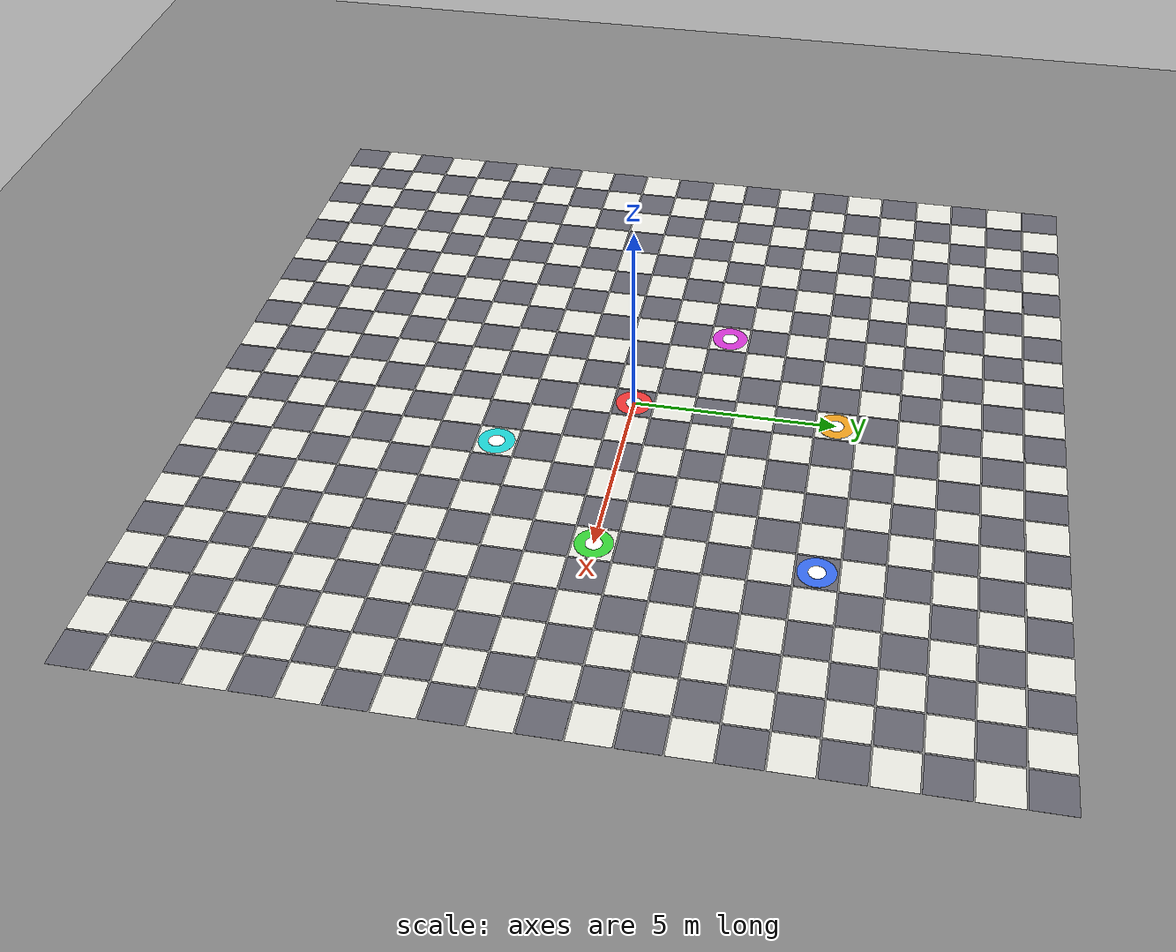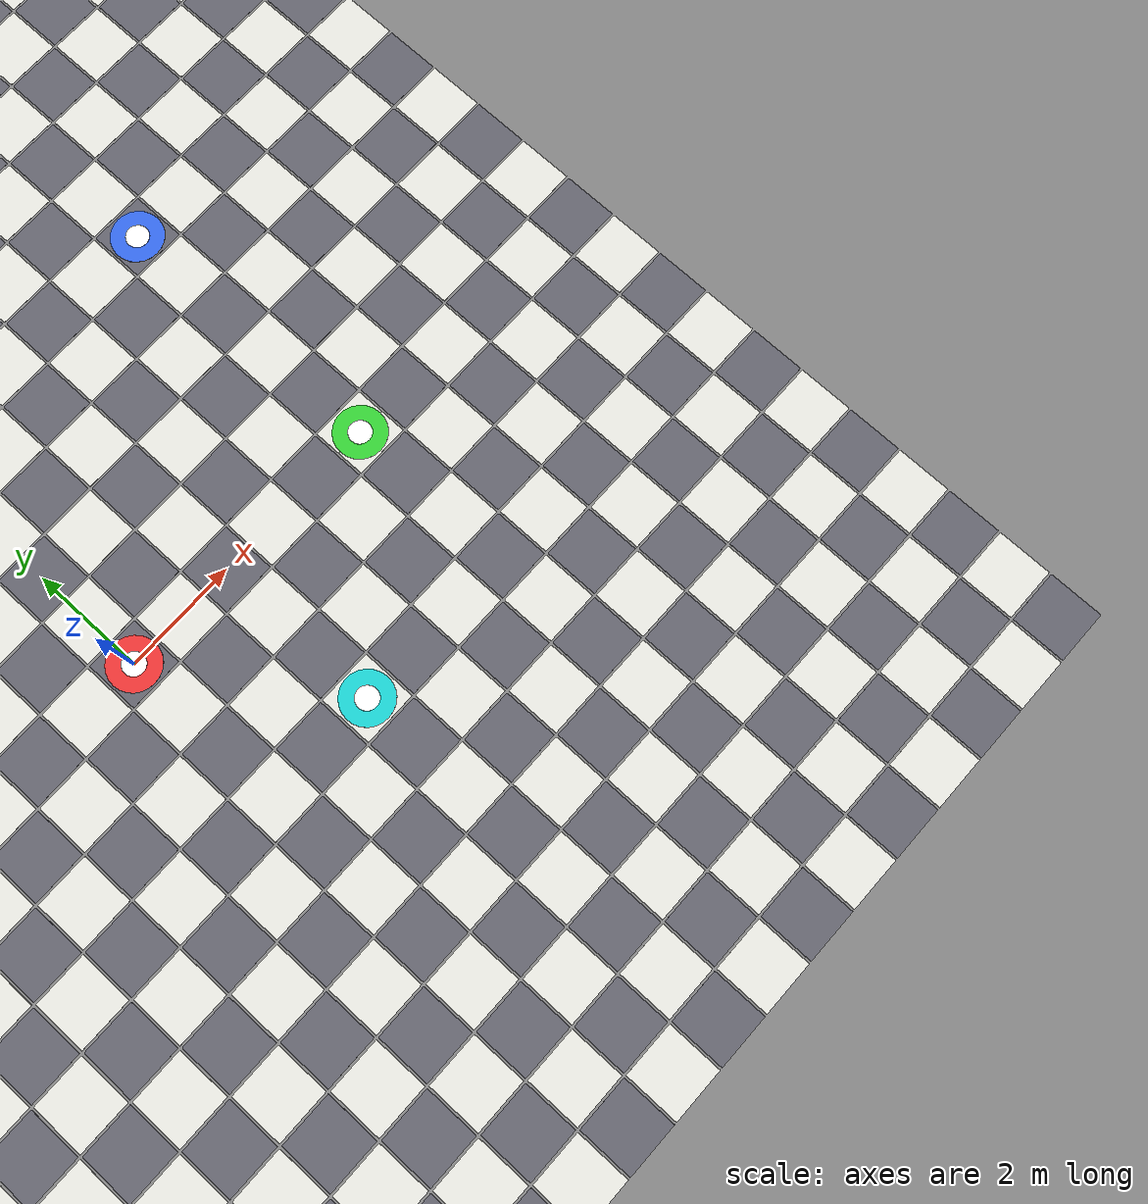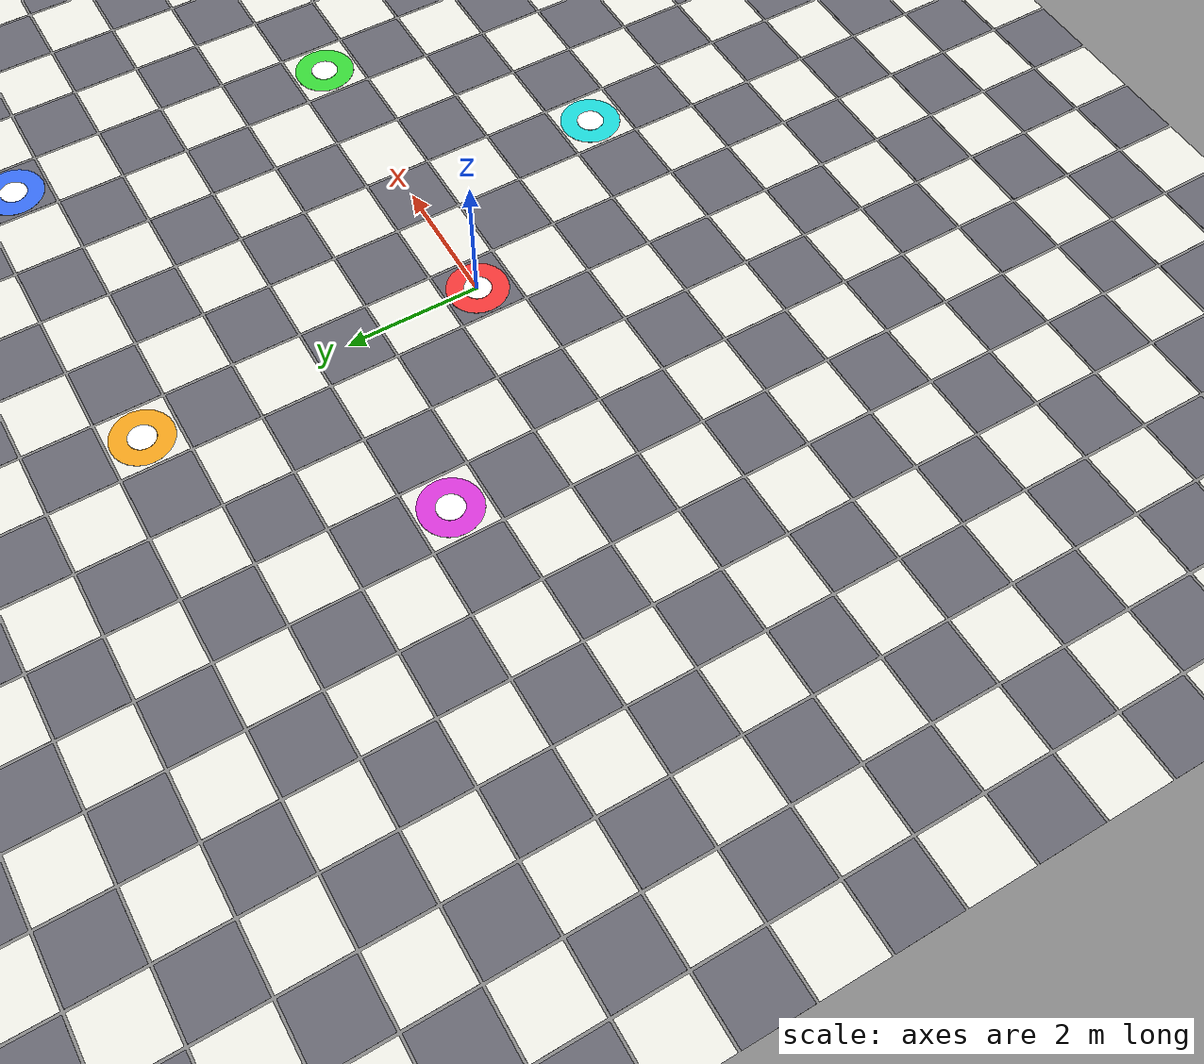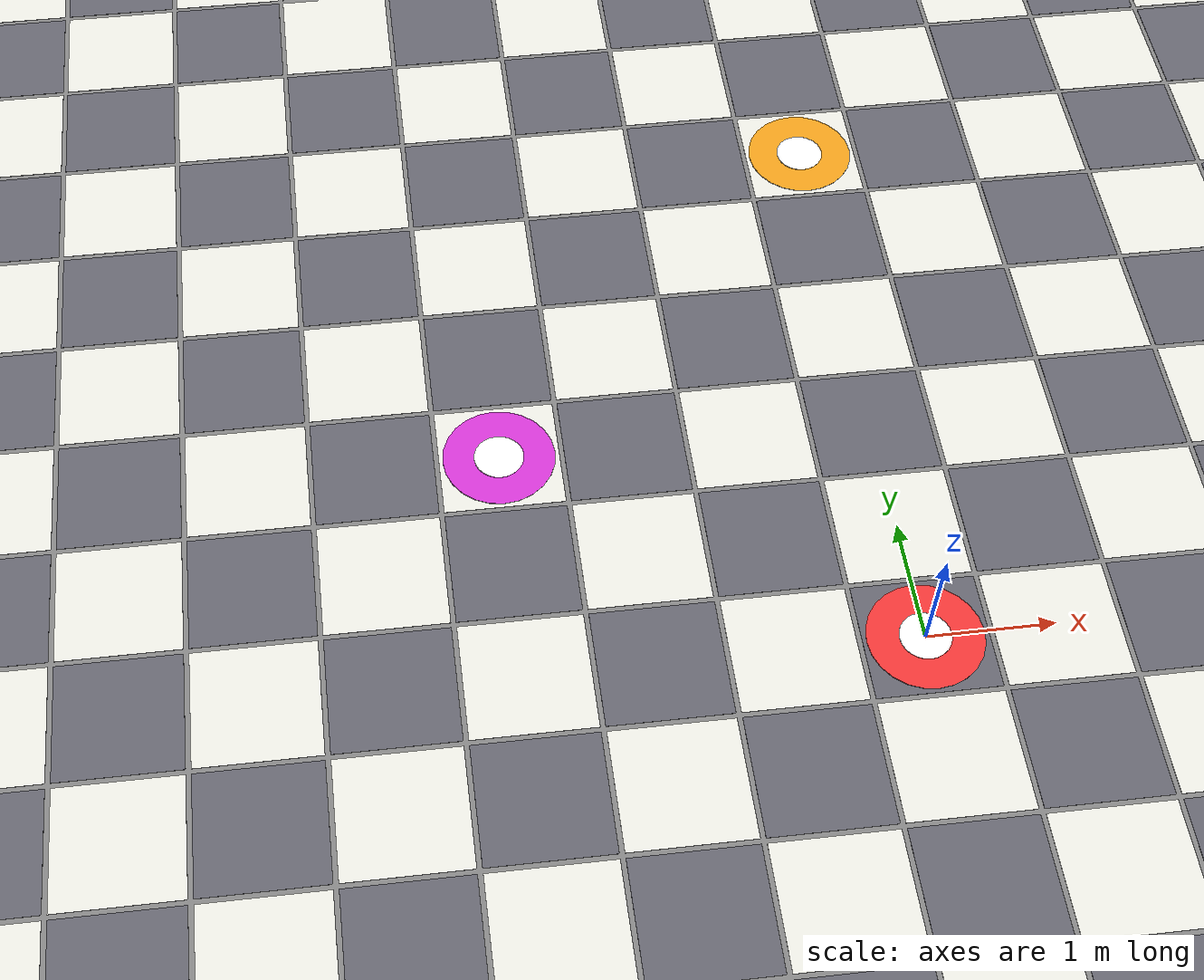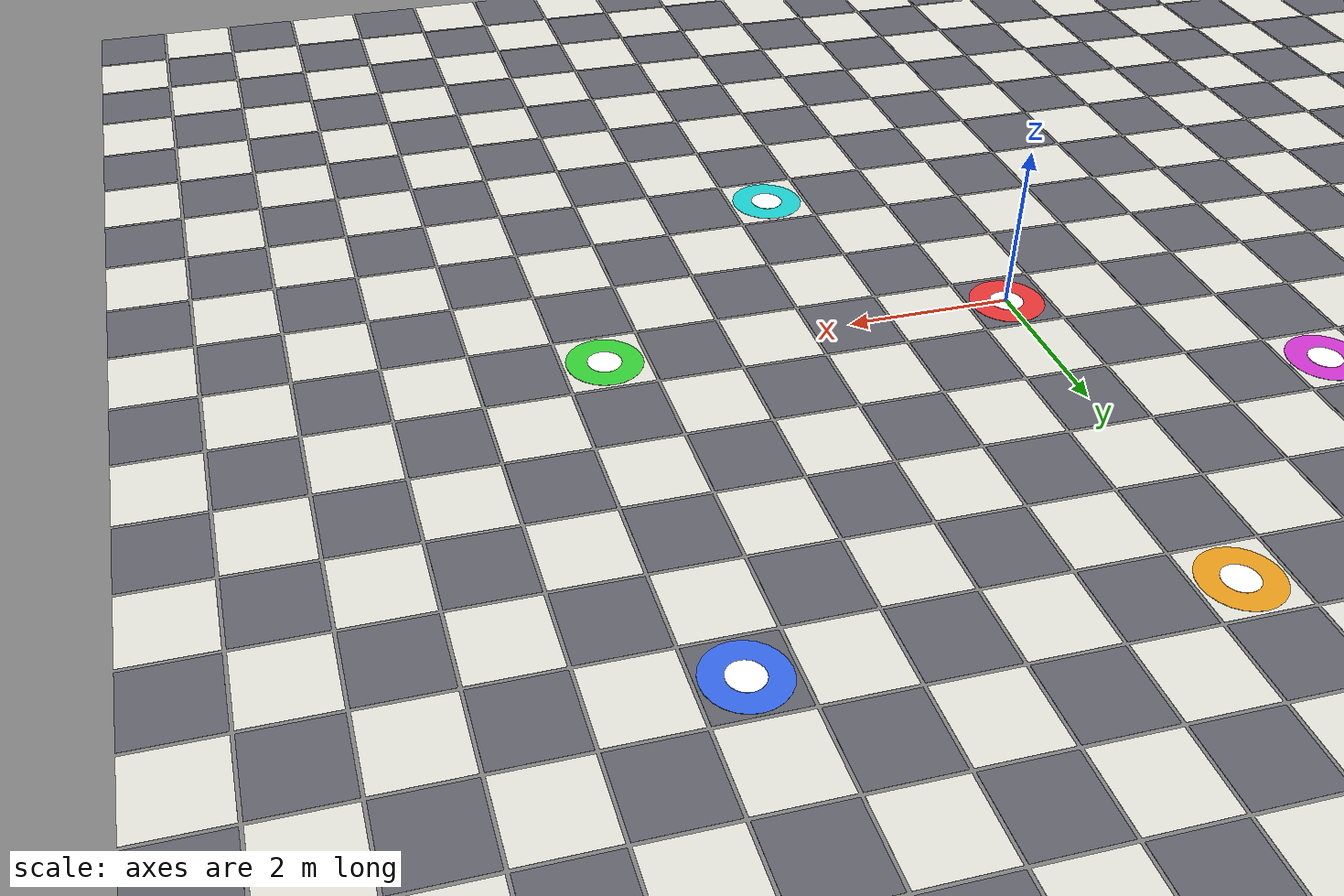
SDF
<sdf version="1.10">
  <world name="empty">
    <physics name="1ms" type="ignored">
      <max_step_size>0.001</max_step_size>
      <real_time_factor>1</real_time_factor>
      <real_time_update_rate>1000</real_time_update_rate>
    </physics>
    <plugin name="gz::sim::systems::Physics" filename="gz-sim-physics-system"/>
    <plugin name="gz::sim::systems::UserCommands" filename="gz-sim-user-commands-system"/>
    <plugin name="gz::sim::systems::SceneBroadcaster" filename="gz-sim-scene-broadcaster-system"/>
    <plugin name="gz::sim::systems::Contact" filename="gz-sim-contact-system"/>
    <plugin name="gz::sim::systems::Sensors" filename="gz-sim-sensors-system">
      <render_engine>ogre2</render_engine>
    </plugin>
    <plugin name="gz::sim::systems::Imu" filename="gz-sim-imu-system"/>

    <gravity>0 0 -9.8</gravity>
    <magnetic_field>5.5645e-06 2.28758e-05 -4.23884e-05</magnetic_field>
    <atmosphere type="adiabatic"/>
    <scene>
      <ambient>0.5 0.5 0.5 1</ambient>
      <background>0.7 0.8 0.9 1</background>
      <shadows>true</shadows>
    </scene>

    <!-- Base Infinite Ground Collision -->
    <model name="ground_plane">
      <static>true</static>
      <link name="link">
        <collision name="collision">
          <geometry>
            <plane>
              <normal>0 0 1</normal>
              <size>100 100</size>
            </plane>
          </geometry>
        </collision>
        <visual name="visual">
          <geometry>
            <plane>
              <normal>0 0 1</normal>
              <size>100 100</size>
            </plane>
          </geometry>
          <material>
            <ambient>0.5 0.5 0.5 1</ambient>
            <diffuse>0.5 0.5 0.5 1</diffuse>
          </material>
        </visual>
      </link>
    </model>

    <!-- Open High-Contrast Textured Floor Grid (20m x 20m, No Walls) -->
    <model name="textured_floor_grid">
      <static>true</static>
      <link name="grid_link">
      <visual name="tile_0_0">
        <pose>-10 -10 0.001 0 0 0</pose>
        <geometry>
          <box><size>0.96 0.96 0.002</size></box>
        </geometry>
        <material>
          <ambient>0.28 0.28 0.32 1</ambient>
          <diffuse>0.38 0.38 0.42 1</diffuse>
          <specular>0.1 0.1 0.1 1</specular>
        </material>
      </visual>
      <visual name="tile_0_1">
        <pose>-10 -9 0.001 0 0 0</pose>
        <geometry>
          <box><size>0.96 0.96 0.002</size></box>
        </geometry>
        <material>
          <ambient>0.78 0.78 0.75 1</ambient>
          <diffuse>0.88 0.88 0.85 1</diffuse>
          <specular>0.1 0.1 0.1 1</specular>
        </material>
      </visual>
      <visual name="tile_0_2">
        <pose>-10 -8 0.001 0 0 0</pose>
        <geometry>
          <box><size>0.96 0.96 0.002</size></box>
        </geometry>
        <material>
          <ambient>0.28 0.28 0.32 1</ambient>
          <diffuse>0.38 0.38 0.42 1</diffuse>
          <specular>0.1 0.1 0.1 1</specular>
        </material>
      </visual>
      <visual name="tile_0_3">
        <pose>-10 -7 0.001 0 0 0</pose>
        <geometry>
          <box><size>0.96 0.96 0.002</size></box>
        </geometry>
        <material>
          <ambient>0.78 0.78 0.75 1</ambient>
          <diffuse>0.88 0.88 0.85 1</diffuse>
          <specular>0.1 0.1 0.1 1</specular>
        </material>
      </visual>
      <visual name="tile_0_4">
        <pose>-10 -6 0.001 0 0 0</pose>
        <geometry>
          <box><size>0.96 0.96 0.002</size></box>
        </geometry>
        <material>
          <ambient>0.28 0.28 0.32 1</ambient>
          <diffuse>0.38 0.38 0.42 1</diffuse>
          <specular>0.1 0.1 0.1 1</specular>
        </material>
      </visual>
      <visual name="tile_0_5">
        <pose>-10 -5 0.001 0 0 0</pose>
        <geometry>
          <box><size>0.96 0.96 0.002</size></box>
        </geometry>
        <material>
          <ambient>0.78 0.78 0.75 1</ambient>
          <diffuse>0.88 0.88 0.85 1</diffuse>
          <specular>0.1 0.1 0.1 1</specular>
        </material>
      </visual>
      <visual name="tile_0_6">
        <pose>-10 -4 0.001 0 0 0</pose>
        <geometry>
          <box><size>0.96 0.96 0.002</size></box>
        </geometry>
        <material>
          <ambient>0.28 0.28 0.32 1</ambient>
          <diffuse>0.38 0.38 0.42 1</diffuse>
          <specular>0.1 0.1 0.1 1</specular>
        </material>
      </visual>
      <visual name="tile_0_7">
        <pose>-10 -3 0.001 0 0 0</pose>
        <geometry>
          <box><size>0.96 0.96 0.002</size></box>
        </geometry>
        <material>
          <ambient>0.78 0.78 0.75 1</ambient>
          <diffuse>0.88 0.88 0.85 1</diffuse>
          <specular>0.1 0.1 0.1 1</specular>
        </material>
      </visual>
      <visual name="tile_0_8">
        <pose>-10 -2 0.001 0 0 0</pose>
        <geometry>
          <box><size>0.96 0.96 0.002</size></box>
        </geometry>
        <material>
          <ambient>0.28 0.28 0.32 1</ambient>
          <diffuse>0.38 0.38 0.42 1</diffuse>
          <specular>0.1 0.1 0.1 1</specular>
        </material>
      </visual>
      <visual name="tile_0_9">
        <pose>-10 -1 0.001 0 0 0</pose>
        <geometry>
          <box><size>0.96 0.96 0.002</size></box>
        </geometry>
        <material>
          <ambient>0.78 0.78 0.75 1</ambient>
          <diffuse>0.88 0.88 0.85 1</diffuse>
          <specular>0.1 0.1 0.1 1</specular>
        </material>
      </visual>
      <visual name="tile_0_10">
        <pose>-10 0 0.001 0 0 0</pose>
        <geometry>
          <box><size>0.96 0.96 0.002</size></box>
        </geometry>
        <material>
          <ambient>0.28 0.28 0.32 1</ambient>
          <diffuse>0.38 0.38 0.42 1</diffuse>
          <specular>0.1 0.1 0.1 1</specular>
        </material>
      </visual>
      <visual name="tile_0_11">
        <pose>-10 1 0.001 0 0 0</pose>
        <geometry>
          <box><size>0.96 0.96 0.002</size></box>
        </geometry>
        <material>
          <ambient>0.78 0.78 0.75 1</ambient>
          <diffuse>0.88 0.88 0.85 1</diffuse>
          <specular>0.1 0.1 0.1 1</specular>
        </material>
      </visual>
      <visual name="tile_0_12">
        <pose>-10 2 0.001 0 0 0</pose>
        <geometry>
          <box><size>0.96 0.96 0.002</size></box>
        </geometry>
        <material>
          <ambient>0.28 0.28 0.32 1</ambient>
          <diffuse>0.38 0.38 0.42 1</diffuse>
          <specular>0.1 0.1 0.1 1</specular>
        </material>
      </visual>
      <visual name="tile_0_13">
        <pose>-10 3 0.001 0 0 0</pose>
        <geometry>
          <box><size>0.96 0.96 0.002</size></box>
        </geometry>
        <material>
          <ambient>0.78 0.78 0.75 1</ambient>
          <diffuse>0.88 0.88 0.85 1</diffuse>
          <specular>0.1 0.1 0.1 1</specular>
        </material>
      </visual>
      <visual name="tile_0_14">
        <pose>-10 4 0.001 0 0 0</pose>
        <geometry>
          <box><size>0.96 0.96 0.002</size></box>
        </geometry>
        <material>
          <ambient>0.28 0.28 0.32 1</ambient>
          <diffuse>0.38 0.38 0.42 1</diffuse>
          <specular>0.1 0.1 0.1 1</specular>
        </material>
      </visual>
      <visual name="tile_0_15">
        <pose>-10 5 0.001 0 0 0</pose>
        <geometry>
          <box><size>0.96 0.96 0.002</size></box>
        </geometry>
        <material>
          <ambient>0.78 0.78 0.75 1</ambient>
          <diffuse>0.88 0.88 0.85 1</diffuse>
          <specular>0.1 0.1 0.1 1</specular>
        </material>
      </visual>
      <visual name="tile_0_16">
        <pose>-10 6 0.001 0 0 0</pose>
        <geometry>
          <box><size>0.96 0.96 0.002</size></box>
        </geometry>
        <material>
          <ambient>0.28 0.28 0.32 1</ambient>
          <diffuse>0.38 0.38 0.42 1</diffuse>
          <specular>0.1 0.1 0.1 1</specular>
        </material>
      </visual>
      <visual name="tile_0_17">
        <pose>-10 7 0.001 0 0 0</pose>
        <geometry>
          <box><size>0.96 0.96 0.002</size></box>
        </geometry>
        <material>
          <ambient>0.78 0.78 0.75 1</ambient>
          <diffuse>0.88 0.88 0.85 1</diffuse>
          <specular>0.1 0.1 0.1 1</specular>
        </material>
      </visual>
      <visual name="tile_0_18">
        <pose>-10 8 0.001 0 0 0</pose>
        <geometry>
          <box><size>0.96 0.96 0.002</size></box>
        </geometry>
        <material>
          <ambient>0.28 0.28 0.32 1</ambient>
          <diffuse>0.38 0.38 0.42 1</diffuse>
          <specular>0.1 0.1 0.1 1</specular>
        </material>
      </visual>
      <visual name="tile_0_19">
        <pose>-10 9 0.001 0 0 0</pose>
        <geometry>
          <box><size>0.96 0.96 0.002</size></box>
        </geometry>
        <material>
          <ambient>0.78 0.78 0.75 1</ambient>
          <diffuse>0.88 0.88 0.85 1</diffuse>
          <specular>0.1 0.1 0.1 1</specular>
        </material>
      </visual>
      <visual name="tile_0_20">
        <pose>-10 10 0.001 0 0 0</pose>
        <geometry>
          <box><size>0.96 0.96 0.002</size></box>
        </geometry>
        <material>
          <ambient>0.28 0.28 0.32 1</ambient>
          <diffuse>0.38 0.38 0.42 1</diffuse>
          <specular>0.1 0.1 0.1 1</specular>
        </material>
      </visual>
      <visual name="tile_1_0">
        <pose>-9 -10 0.001 0 0 0</pose>
        <geometry>
          <box><size>0.96 0.96 0.002</size></box>
        </geometry>
        <material>
          <ambient>0.78 0.78 0.75 1</ambient>
          <diffuse>0.88 0.88 0.85 1</diffuse>
          <specular>0.1 0.1 0.1 1</specular>
        </material>
      </visual>
      <visual name="tile_1_1">
        <pose>-9 -9 0.001 0 0 0</pose>
        <geometry>
          <box><size>0.96 0.96 0.002</size></box>
        </geometry>
        <material>
          <ambient>0.28 0.28 0.32 1</ambient>
          <diffuse>0.38 0.38 0.42 1</diffuse>
          <specular>0.1 0.1 0.1 1</specular>
        </material>
      </visual>
      <visual name="tile_1_2">
        <pose>-9 -8 0.001 0 0 0</pose>
        <geometry>
          <box><size>0.96 0.96 0.002</size></box>
        </geometry>
        <material>
          <ambient>0.78 0.78 0.75 1</ambient>
          <diffuse>0.88 0.88 0.85 1</diffuse>
          <specular>0.1 0.1 0.1 1</specular>
        </material>
      </visual>
      <visual name="tile_1_3">
        <pose>-9 -7 0.001 0 0 0</pose>
        <geometry>
          <box><size>0.96 0.96 0.002</size></box>
        </geometry>
        <material>
          <ambient>0.28 0.28 0.32 1</ambient>
          <diffuse>0.38 0.38 0.42 1</diffuse>
          <specular>0.1 0.1 0.1 1</specular>
        </material>
      </visual>
      <visual name="tile_1_4">
        <pose>-9 -6 0.001 0 0 0</pose>
        <geometry>
          <box><size>0.96 0.96 0.002</size></box>
        </geometry>
        <material>
          <ambient>0.78 0.78 0.75 1</ambient>
          <diffuse>0.88 0.88 0.85 1</diffuse>
          <specular>0.1 0.1 0.1 1</specular>
        </material>
      </visual>
      <visual name="tile_1_5">
        <pose>-9 -5 0.001 0 0 0</pose>
        <geometry>
          <box><size>0.96 0.96 0.002</size></box>
        </geometry>
        <material>
          <ambient>0.28 0.28 0.32 1</ambient>
          <diffuse>0.38 0.38 0.42 1</diffuse>
          <specular>0.1 0.1 0.1 1</specular>
        </material>
      </visual>
      <visual name="tile_1_6">
        <pose>-9 -4 0.001 0 0 0</pose>
        <geometry>
          <box><size>0.96 0.96 0.002</size></box>
        </geometry>
        <material>
          <ambient>0.78 0.78 0.75 1</ambient>
          <diffuse>0.88 0.88 0.85 1</diffuse>
          <specular>0.1 0.1 0.1 1</specular>
        </material>
      </visual>
      <visual name="tile_1_7">
        <pose>-9 -3 0.001 0 0 0</pose>
        <geometry>
          <box><size>0.96 0.96 0.002</size></box>
        </geometry>
        <material>
          <ambient>0.28 0.28 0.32 1</ambient>
          <diffuse>0.38 0.38 0.42 1</diffuse>
          <specular>0.1 0.1 0.1 1</specular>
        </material>
      </visual>
      <visual name="tile_1_8">
        <pose>-9 -2 0.001 0 0 0</pose>
        <geometry>
          <box><size>0.96 0.96 0.002</size></box>
        </geometry>
        <material>
          <ambient>0.78 0.78 0.75 1</ambient>
          <diffuse>0.88 0.88 0.85 1</diffuse>
          <specular>0.1 0.1 0.1 1</specular>
        </material>
      </visual>
      <visual name="tile_1_9">
        <pose>-9 -1 0.001 0 0 0</pose>
        <geometry>
          <box><size>0.96 0.96 0.002</size></box>
        </geometry>
        <material>
          <ambient>0.28 0.28 0.32 1</ambient>
          <diffuse>0.38 0.38 0.42 1</diffuse>
          <specular>0.1 0.1 0.1 1</specular>
        </material>
      </visual>
      <visual name="tile_1_10">
        <pose>-9 0 0.001 0 0 0</pose>
        <geometry>
          <box><size>0.96 0.96 0.002</size></box>
        </geometry>
        <material>
          <ambient>0.78 0.78 0.75 1</ambient>
          <diffuse>0.88 0.88 0.85 1</diffuse>
          <specular>0.1 0.1 0.1 1</specular>
        </material>
      </visual>
      <visual name="tile_1_11">
        <pose>-9 1 0.001 0 0 0</pose>
        <geometry>
          <box><size>0.96 0.96 0.002</size></box>
        </geometry>
        <material>
          <ambient>0.28 0.28 0.32 1</ambient>
          <diffuse>0.38 0.38 0.42 1</diffuse>
          <specular>0.1 0.1 0.1 1</specular>
        </material>
      </visual>
      <visual name="tile_1_12">
        <pose>-9 2 0.001 0 0 0</pose>
        <geometry>
          <box><size>0.96 0.96 0.002</size></box>
        </geometry>
        <material>
          <ambient>0.78 0.78 0.75 1</ambient>
          <diffuse>0.88 0.88 0.85 1</diffuse>
          <specular>0.1 0.1 0.1 1</specular>
        </material>
      </visual>
      <visual name="tile_1_13">
        <pose>-9 3 0.001 0 0 0</pose>
        <geometry>
          <box><size>0.96 0.96 0.002</size></box>
        </geometry>
        <material>
          <ambient>0.28 0.28 0.32 1</ambient>
          <diffuse>0.38 0.38 0.42 1</diffuse>
          <specular>0.1 0.1 0.1 1</specular>
        </material>
      </visual>
      <visual name="tile_1_14">
        <pose>-9 4 0.001 0 0 0</pose>
        <geometry>
          <box><size>0.96 0.96 0.002</size></box>
        </geometry>
        <material>
          <ambient>0.78 0.78 0.75 1</ambient>
          <diffuse>0.88 0.88 0.85 1</diffuse>
          <specular>0.1 0.1 0.1 1</specular>
        </material>
      </visual>
      <visual name="tile_1_15">
        <pose>-9 5 0.001 0 0 0</pose>
        <geometry>
          <box><size>0.96 0.96 0.002</size></box>
        </geometry>
        <material>
          <ambient>0.28 0.28 0.32 1</ambient>
          <diffuse>0.38 0.38 0.42 1</diffuse>
          <specular>0.1 0.1 0.1 1</specular>
        </material>
      </visual>
      <visual name="tile_1_16">
        <pose>-9 6 0.001 0 0 0</pose>
        <geometry>
          <box><size>0.96 0.96 0.002</size></box>
        </geometry>
        <material>
          <ambient>0.78 0.78 0.75 1</ambient>
          <diffuse>0.88 0.88 0.85 1</diffuse>
          <specular>0.1 0.1 0.1 1</specular>
        </material>
      </visual>
      <visual name="tile_1_17">
        <pose>-9 7 0.001 0 0 0</pose>
        <geometry>
          <box><size>0.96 0.96 0.002</size></box>
        </geometry>
        <material>
          <ambient>0.28 0.28 0.32 1</ambient>
          <diffuse>0.38 0.38 0.42 1</diffuse>
          <specular>0.1 0.1 0.1 1</specular>
        </material>
      </visual>
      <visual name="tile_1_18">
        <pose>-9 8 0.001 0 0 0</pose>
        <geometry>
          <box><size>0.96 0.96 0.002</size></box>
        </geometry>
        <material>
          <ambient>0.78 0.78 0.75 1</ambient>
          <diffuse>0.88 0.88 0.85 1</diffuse>
          <specular>0.1 0.1 0.1 1</specular>
        </material>
      </visual>
      <visual name="tile_1_19">
        <pose>-9 9 0.001 0 0 0</pose>
        <geometry>
          <box><size>0.96 0.96 0.002</size></box>
        </geometry>
        <material>
          <ambient>0.28 0.28 0.32 1</ambient>
          <diffuse>0.38 0.38 0.42 1</diffuse>
          <specular>0.1 0.1 0.1 1</specular>
        </material>
      </visual>
      <visual name="tile_1_20">
        <pose>-9 10 0.001 0 0 0</pose>
        <geometry>
          <box><size>0.96 0.96 0.002</size></box>
        </geometry>
        <material>
          <ambient>0.78 0.78 0.75 1</ambient>
          <diffuse>0.88 0.88 0.85 1</diffuse>
          <specular>0.1 0.1 0.1 1</specular>
        </material>
      </visual>
      <visual name="tile_2_0">
        <pose>-8 -10 0.001 0 0 0</pose>
        <geometry>
          <box><size>0.96 0.96 0.002</size></box>
        </geometry>
        <material>
          <ambient>0.28 0.28 0.32 1</ambient>
          <diffuse>0.38 0.38 0.42 1</diffuse>
          <specular>0.1 0.1 0.1 1</specular>
        </material>
      </visual>
      <visual name="tile_2_1">
        <pose>-8 -9 0.001 0 0 0</pose>
        <geometry>
          <box><size>0.96 0.96 0.002</size></box>
        </geometry>
        <material>
          <ambient>0.78 0.78 0.75 1</ambient>
          <diffuse>0.88 0.88 0.85 1</diffuse>
          <specular>0.1 0.1 0.1 1</specular>
        </material>
      </visual>
      <visual name="tile_2_2">
        <pose>-8 -8 0.001 0 0 0</pose>
        <geometry>
          <box><size>0.96 0.96 0.002</size></box>
        </geometry>
        <material>
          <ambient>0.28 0.28 0.32 1</ambient>
          <diffuse>0.38 0.38 0.42 1</diffuse>
          <specular>0.1 0.1 0.1 1</specular>
        </material>
      </visual>
      <visual name="tile_2_3">
        <pose>-8 -7 0.001 0 0 0</pose>
        <geometry>
          <box><size>0.96 0.96 0.002</size></box>
        </geometry>
        <material>
          <ambient>0.78 0.78 0.75 1</ambient>
          <diffuse>0.88 0.88 0.85 1</diffuse>
          <specular>0.1 0.1 0.1 1</specular>
        </material>
      </visual>
      <visual name="tile_2_4">
        <pose>-8 -6 0.001 0 0 0</pose>
        <geometry>
          <box><size>0.96 0.96 0.002</size></box>
        </geometry>
        <material>
          <ambient>0.28 0.28 0.32 1</ambient>
          <diffuse>0.38 0.38 0.42 1</diffuse>
          <specular>0.1 0.1 0.1 1</specular>
        </material>
      </visual>
      <visual name="tile_2_5">
        <pose>-8 -5 0.001 0 0 0</pose>
        <geometry>
          <box><size>0.96 0.96 0.002</size></box>
        </geometry>
        <material>
          <ambient>0.78 0.78 0.75 1</ambient>
          <diffuse>0.88 0.88 0.85 1</diffuse>
          <specular>0.1 0.1 0.1 1</specular>
        </material>
      </visual>
      <visual name="tile_2_6">
        <pose>-8 -4 0.001 0 0 0</pose>
        <geometry>
          <box><size>0.96 0.96 0.002</size></box>
        </geometry>
        <material>
          <ambient>0.28 0.28 0.32 1</ambient>
          <diffuse>0.38 0.38 0.42 1</diffuse>
          <specular>0.1 0.1 0.1 1</specular>
        </material>
      </visual>
      <visual name="tile_2_7">
        <pose>-8 -3 0.001 0 0 0</pose>
        <geometry>
          <box><size>0.96 0.96 0.002</size></box>
        </geometry>
        <material>
          <ambient>0.78 0.78 0.75 1</ambient>
          <diffuse>0.88 0.88 0.85 1</diffuse>
          <specular>0.1 0.1 0.1 1</specular>
        </material>
      </visual>
      <visual name="tile_2_8">
        <pose>-8 -2 0.001 0 0 0</pose>
        <geometry>
          <box><size>0.96 0.96 0.002</size></box>
        </geometry>
        <material>
          <ambient>0.28 0.28 0.32 1</ambient>
          <diffuse>0.38 0.38 0.42 1</diffuse>
          <specular>0.1 0.1 0.1 1</specular>
        </material>
      </visual>
      <visual name="tile_2_9">
        <pose>-8 -1 0.001 0 0 0</pose>
        <geometry>
          <box><size>0.96 0.96 0.002</size></box>
        </geometry>
        <material>
          <ambient>0.78 0.78 0.75 1</ambient>
          <diffuse>0.88 0.88 0.85 1</diffuse>
          <specular>0.1 0.1 0.1 1</specular>
        </material>
      </visual>
      <visual name="tile_2_10">
        <pose>-8 0 0.001 0 0 0</pose>
        <geometry>
          <box><size>0.96 0.96 0.002</size></box>
        </geometry>
        <material>
          <ambient>0.28 0.28 0.32 1</ambient>
          <diffuse>0.38 0.38 0.42 1</diffuse>
          <specular>0.1 0.1 0.1 1</specular>
        </material>
      </visual>
      <visual name="tile_2_11">
        <pose>-8 1 0.001 0 0 0</pose>
        <geometry>
          <box><size>0.96 0.96 0.002</size></box>
        </geometry>
        <material>
          <ambient>0.78 0.78 0.75 1</ambient>
          <diffuse>0.88 0.88 0.85 1</diffuse>
          <specular>0.1 0.1 0.1 1</specular>
        </material>
      </visual>
      <visual name="tile_2_12">
        <pose>-8 2 0.001 0 0 0</pose>
        <geometry>
          <box><size>0.96 0.96 0.002</size></box>
        </geometry>
        <material>
          <ambient>0.28 0.28 0.32 1</ambient>
          <diffuse>0.38 0.38 0.42 1</diffuse>
          <specular>0.1 0.1 0.1 1</specular>
        </material>
      </visual>
      <visual name="tile_2_13">
        <pose>-8 3 0.001 0 0 0</pose>
        <geometry>
          <box><size>0.96 0.96 0.002</size></box>
        </geometry>
        <material>
          <ambient>0.78 0.78 0.75 1</ambient>
          <diffuse>0.88 0.88 0.85 1</diffuse>
          <specular>0.1 0.1 0.1 1</specular>
        </material>
      </visual>
      <visual name="tile_2_14">
        <pose>-8 4 0.001 0 0 0</pose>
        <geometry>
          <box><size>0.96 0.96 0.002</size></box>
        </geometry>
        <material>
          <ambient>0.28 0.28 0.32 1</ambient>
          <diffuse>0.38 0.38 0.42 1</diffuse>
          <specular>0.1 0.1 0.1 1</specular>
        </material>
      </visual>
      <visual name="tile_2_15">
        <pose>-8 5 0.001 0 0 0</pose>
        <geometry>
          <box><size>0.96 0.96 0.002</size></box>
        </geometry>
        <material>
          <ambient>0.78 0.78 0.75 1</ambient>
          <diffuse>0.88 0.88 0.85 1</diffuse>
          <specular>0.1 0.1 0.1 1</specular>
        </material>
      </visual>
      <visual name="tile_2_16">
        <pose>-8 6 0.001 0 0 0</pose>
        <geometry>
          <box><size>0.96 0.96 0.002</size></box>
        </geometry>
        <material>
          <ambient>0.28 0.28 0.32 1</ambient>
          <diffuse>0.38 0.38 0.42 1</diffuse>
          <specular>0.1 0.1 0.1 1</specular>
        </material>
      </visual>
      <visual name="tile_2_17">
        <pose>-8 7 0.001 0 0 0</pose>
        <geometry>
          <box><size>0.96 0.96 0.002</size></box>
        </geometry>
        <material>
          <ambient>0.78 0.78 0.75 1</ambient>
          <diffuse>0.88 0.88 0.85 1</diffuse>
          <specular>0.1 0.1 0.1 1</specular>
        </material>
      </visual>
      <visual name="tile_2_18">
        <pose>-8 8 0.001 0 0 0</pose>
        <geometry>
          <box><size>0.96 0.96 0.002</size></box>
        </geometry>
        <material>
          <ambient>0.28 0.28 0.32 1</ambient>
          <diffuse>0.38 0.38 0.42 1</diffuse>
          <specular>0.1 0.1 0.1 1</specular>
        </material>
      </visual>
      <visual name="tile_2_19">
        <pose>-8 9 0.001 0 0 0</pose>
        <geometry>
          <box><size>0.96 0.96 0.002</size></box>
        </geometry>
        <material>
          <ambient>0.78 0.78 0.75 1</ambient>
          <diffuse>0.88 0.88 0.85 1</diffuse>
          <specular>0.1 0.1 0.1 1</specular>
        </material>
      </visual>
      <visual name="tile_2_20">
        <pose>-8 10 0.001 0 0 0</pose>
        <geometry>
          <box><size>0.96 0.96 0.002</size></box>
        </geometry>
        <material>
          <ambient>0.28 0.28 0.32 1</ambient>
          <diffuse>0.38 0.38 0.42 1</diffuse>
          <specular>0.1 0.1 0.1 1</specular>
        </material>
      </visual>
      <visual name="tile_3_0">
        <pose>-7 -10 0.001 0 0 0</pose>
        <geometry>
          <box><size>0.96 0.96 0.002</size></box>
        </geometry>
        <material>
          <ambient>0.78 0.78 0.75 1</ambient>
          <diffuse>0.88 0.88 0.85 1</diffuse>
          <specular>0.1 0.1 0.1 1</specular>
        </material>
      </visual>
      <visual name="tile_3_1">
        <pose>-7 -9 0.001 0 0 0</pose>
        <geometry>
          <box><size>0.96 0.96 0.002</size></box>
        </geometry>
        <material>
          <ambient>0.28 0.28 0.32 1</ambient>
          <diffuse>0.38 0.38 0.42 1</diffuse>
          <specular>0.1 0.1 0.1 1</specular>
        </material>
      </visual>
      <visual name="tile_3_2">
        <pose>-7 -8 0.001 0 0 0</pose>
        <geometry>
          <box><size>0.96 0.96 0.002</size></box>
        </geometry>
        <material>
          <ambient>0.78 0.78 0.75 1</ambient>
          <diffuse>0.88 0.88 0.85 1</diffuse>
          <specular>0.1 0.1 0.1 1</specular>
        </material>
      </visual>
      <visual name="tile_3_3">
        <pose>-7 -7 0.001 0 0 0</pose>
        <geometry>
          <box><size>0.96 0.96 0.002</size></box>
        </geometry>
        <material>
          <ambient>0.28 0.28 0.32 1</ambient>
          <diffuse>0.38 0.38 0.42 1</diffuse>
          <specular>0.1 0.1 0.1 1</specular>
        </material>
      </visual>
      <visual name="tile_3_4">
        <pose>-7 -6 0.001 0 0 0</pose>
        <geometry>
          <box><size>0.96 0.96 0.002</size></box>
        </geometry>
        <material>
          <ambient>0.78 0.78 0.75 1</ambient>
          <diffuse>0.88 0.88 0.85 1</diffuse>
          <specular>0.1 0.1 0.1 1</specular>
        </material>
      </visual>
      <visual name="tile_3_5">
        <pose>-7 -5 0.001 0 0 0</pose>
        <geometry>
          <box><size>0.96 0.96 0.002</size></box>
        </geometry>
        <material>
          <ambient>0.28 0.28 0.32 1</ambient>
          <diffuse>0.38 0.38 0.42 1</diffuse>
          <specular>0.1 0.1 0.1 1</specular>
        </material>
      </visual>
      <visual name="tile_3_6">
        <pose>-7 -4 0.001 0 0 0</pose>
        <geometry>
          <box><size>0.96 0.96 0.002</size></box>
        </geometry>
        <material>
          <ambient>0.78 0.78 0.75 1</ambient>
          <diffuse>0.88 0.88 0.85 1</diffuse>
          <specular>0.1 0.1 0.1 1</specular>
        </material>
      </visual>
      <visual name="tile_3_7">
        <pose>-7 -3 0.001 0 0 0</pose>
        <geometry>
          <box><size>0.96 0.96 0.002</size></box>
        </geometry>
        <material>
          <ambient>0.28 0.28 0.32 1</ambient>
          <diffuse>0.38 0.38 0.42 1</diffuse>
          <specular>0.1 0.1 0.1 1</specular>
        </material>
      </visual>
      <visual name="tile_3_8">
        <pose>-7 -2 0.001 0 0 0</pose>
        <geometry>
          <box><size>0.96 0.96 0.002</size></box>
        </geometry>
        <material>
          <ambient>0.78 0.78 0.75 1</ambient>
          <diffuse>0.88 0.88 0.85 1</diffuse>
          <specular>0.1 0.1 0.1 1</specular>
        </material>
      </visual>
      <visual name="tile_3_9">
        <pose>-7 -1 0.001 0 0 0</pose>
        <geometry>
          <box><size>0.96 0.96 0.002</size></box>
        </geometry>
        <material>
          <ambient>0.28 0.28 0.32 1</ambient>
          <diffuse>0.38 0.38 0.42 1</diffuse>
          <specular>0.1 0.1 0.1 1</specular>
        </material>
      </visual>
      <visual name="tile_3_10">
        <pose>-7 0 0.001 0 0 0</pose>
        <geometry>
          <box><size>0.96 0.96 0.002</size></box>
        </geometry>
        <material>
          <ambient>0.78 0.78 0.75 1</ambient>
          <diffuse>0.88 0.88 0.85 1</diffuse>
          <specular>0.1 0.1 0.1 1</specular>
        </material>
      </visual>
      <visual name="tile_3_11">
        <pose>-7 1 0.001 0 0 0</pose>
        <geometry>
          <box><size>0.96 0.96 0.002</size></box>
        </geometry>
        <material>
          <ambient>0.28 0.28 0.32 1</ambient>
          <diffuse>0.38 0.38 0.42 1</diffuse>
          <specular>0.1 0.1 0.1 1</specular>
        </material>
      </visual>
      <visual name="tile_3_12">
        <pose>-7 2 0.001 0 0 0</pose>
        <geometry>
          <box><size>0.96 0.96 0.002</size></box>
        </geometry>
        <material>
          <ambient>0.78 0.78 0.75 1</ambient>
          <diffuse>0.88 0.88 0.85 1</diffuse>
          <specular>0.1 0.1 0.1 1</specular>
        </material>
      </visual>
      <visual name="tile_3_13">
        <pose>-7 3 0.001 0 0 0</pose>
        <geometry>
          <box><size>0.96 0.96 0.002</size></box>
        </geometry>
        <material>
          <ambient>0.28 0.28 0.32 1</ambient>
          <diffuse>0.38 0.38 0.42 1</diffuse>
          <specular>0.1 0.1 0.1 1</specular>
        </material>
      </visual>
      <visual name="tile_3_14">
        <pose>-7 4 0.001 0 0 0</pose>
        <geometry>
          <box><size>0.96 0.96 0.002</size></box>
        </geometry>
        <material>
          <ambient>0.78 0.78 0.75 1</ambient>
          <diffuse>0.88 0.88 0.85 1</diffuse>
          <specular>0.1 0.1 0.1 1</specular>
        </material>
      </visual>
      <visual name="tile_3_15">
        <pose>-7 5 0.001 0 0 0</pose>
        <geometry>
          <box><size>0.96 0.96 0.002</size></box>
        </geometry>
        <material>
          <ambient>0.28 0.28 0.32 1</ambient>
          <diffuse>0.38 0.38 0.42 1</diffuse>
          <specular>0.1 0.1 0.1 1</specular>
        </material>
      </visual>
      <visual name="tile_3_16">
        <pose>-7 6 0.001 0 0 0</pose>
        <geometry>
          <box><size>0.96 0.96 0.002</size></box>
        </geometry>
        <material>
          <ambient>0.78 0.78 0.75 1</ambient>
          <diffuse>0.88 0.88 0.85 1</diffuse>
          <specular>0.1 0.1 0.1 1</specular>
        </material>
      </visual>
      <visual name="tile_3_17">
        <pose>-7 7 0.001 0 0 0</pose>
        <geometry>
          <box><size>0.96 0.96 0.002</size></box>
        </geometry>
        <material>
          <ambient>0.28 0.28 0.32 1</ambient>
          <diffuse>0.38 0.38 0.42 1</diffuse>
          <specular>0.1 0.1 0.1 1</specular>
        </material>
      </visual>
      <visual name="tile_3_18">
        <pose>-7 8 0.001 0 0 0</pose>
        <geometry>
          <box><size>0.96 0.96 0.002</size></box>
        </geometry>
        <material>
          <ambient>0.78 0.78 0.75 1</ambient>
          <diffuse>0.88 0.88 0.85 1</diffuse>
          <specular>0.1 0.1 0.1 1</specular>
        </material>
      </visual>
      <visual name="tile_3_19">
        <pose>-7 9 0.001 0 0 0</pose>
        <geometry>
          <box><size>0.96 0.96 0.002</size></box>
        </geometry>
        <material>
          <ambient>0.28 0.28 0.32 1</ambient>
          <diffuse>0.38 0.38 0.42 1</diffuse>
          <specular>0.1 0.1 0.1 1</specular>
        </material>
      </visual>
      <visual name="tile_3_20">
        <pose>-7 10 0.001 0 0 0</pose>
        <geometry>
          <box><size>0.96 0.96 0.002</size></box>
        </geometry>
        <material>
          <ambient>0.78 0.78 0.75 1</ambient>
          <diffuse>0.88 0.88 0.85 1</diffuse>
          <specular>0.1 0.1 0.1 1</specular>
        </material>
      </visual>
      <visual name="tile_4_0">
        <pose>-6 -10 0.001 0 0 0</pose>
        <geometry>
          <box><size>0.96 0.96 0.002</size></box>
        </geometry>
        <material>
          <ambient>0.28 0.28 0.32 1</ambient>
          <diffuse>0.38 0.38 0.42 1</diffuse>
          <specular>0.1 0.1 0.1 1</specular>
        </material>
      </visual>
      <visual name="tile_4_1">
        <pose>-6 -9 0.001 0 0 0</pose>
        <geometry>
          <box><size>0.96 0.96 0.002</size></box>
        </geometry>
        <material>
          <ambient>0.78 0.78 0.75 1</ambient>
          <diffuse>0.88 0.88 0.85 1</diffuse>
          <specular>0.1 0.1 0.1 1</specular>
        </material>
      </visual>
      <visual name="tile_4_2">
        <pose>-6 -8 0.001 0 0 0</pose>
        <geometry>
          <box><size>0.96 0.96 0.002</size></box>
        </geometry>
        <material>
          <ambient>0.28 0.28 0.32 1</ambient>
          <diffuse>0.38 0.38 0.42 1</diffuse>
          <specular>0.1 0.1 0.1 1</specular>
        </material>
      </visual>
      <visual name="tile_4_3">
        <pose>-6 -7 0.001 0 0 0</pose>
        <geometry>
          <box><size>0.96 0.96 0.002</size></box>
        </geometry>
        <material>
          <ambient>0.78 0.78 0.75 1</ambient>
          <diffuse>0.88 0.88 0.85 1</diffuse>
          <specular>0.1 0.1 0.1 1</specular>
        </material>
      </visual>
      <visual name="tile_4_4">
        <pose>-6 -6 0.001 0 0 0</pose>
        <geometry>
          <box><size>0.96 0.96 0.002</size></box>
        </geometry>
        <material>
          <ambient>0.28 0.28 0.32 1</ambient>
          <diffuse>0.38 0.38 0.42 1</diffuse>
          <specular>0.1 0.1 0.1 1</specular>
        </material>
      </visual>
      <visual name="tile_4_5">
        <pose>-6 -5 0.001 0 0 0</pose>
        <geometry>
          <box><size>0.96 0.96 0.002</size></box>
        </geometry>
        <material>
          <ambient>0.78 0.78 0.75 1</ambient>
          <diffuse>0.88 0.88 0.85 1</diffuse>
          <specular>0.1 0.1 0.1 1</specular>
        </material>
      </visual>
      <visual name="tile_4_6">
        <pose>-6 -4 0.001 0 0 0</pose>
        <geometry>
          <box><size>0.96 0.96 0.002</size></box>
        </geometry>
        <material>
          <ambient>0.28 0.28 0.32 1</ambient>
          <diffuse>0.38 0.38 0.42 1</diffuse>
          <specular>0.1 0.1 0.1 1</specular>
        </material>
      </visual>
      <visual name="tile_4_7">
        <pose>-6 -3 0.001 0 0 0</pose>
        <geometry>
          <box><size>0.96 0.96 0.002</size></box>
        </geometry>
        <material>
          <ambient>0.78 0.78 0.75 1</ambient>
          <diffuse>0.88 0.88 0.85 1</diffuse>
          <specular>0.1 0.1 0.1 1</specular>
        </material>
      </visual>
      <visual name="tile_4_8">
        <pose>-6 -2 0.001 0 0 0</pose>
        <geometry>
          <box><size>0.96 0.96 0.002</size></box>
        </geometry>
        <material>
          <ambient>0.28 0.28 0.32 1</ambient>
          <diffuse>0.38 0.38 0.42 1</diffuse>
          <specular>0.1 0.1 0.1 1</specular>
        </material>
      </visual>
      <visual name="tile_4_9">
        <pose>-6 -1 0.001 0 0 0</pose>
        <geometry>
          <box><size>0.96 0.96 0.002</size></box>
        </geometry>
        <material>
          <ambient>0.78 0.78 0.75 1</ambient>
          <diffuse>0.88 0.88 0.85 1</diffuse>
          <specular>0.1 0.1 0.1 1</specular>
        </material>
      </visual>
      <visual name="tile_4_10">
        <pose>-6 0 0.001 0 0 0</pose>
        <geometry>
          <box><size>0.96 0.96 0.002</size></box>
        </geometry>
        <material>
          <ambient>0.28 0.28 0.32 1</ambient>
          <diffuse>0.38 0.38 0.42 1</diffuse>
          <specular>0.1 0.1 0.1 1</specular>
        </material>
      </visual>
      <visual name="tile_4_11">
        <pose>-6 1 0.001 0 0 0</pose>
        <geometry>
          <box><size>0.96 0.96 0.002</size></box>
        </geometry>
        <material>
          <ambient>0.78 0.78 0.75 1</ambient>
          <diffuse>0.88 0.88 0.85 1</diffuse>
          <specular>0.1 0.1 0.1 1</specular>
        </material>
      </visual>
      <visual name="tile_4_12">
        <pose>-6 2 0.001 0 0 0</pose>
        <geometry>
          <box><size>0.96 0.96 0.002</size></box>
        </geometry>
        <material>
          <ambient>0.28 0.28 0.32 1</ambient>
          <diffuse>0.38 0.38 0.42 1</diffuse>
          <specular>0.1 0.1 0.1 1</specular>
        </material>
      </visual>
      <visual name="tile_4_13">
        <pose>-6 3 0.001 0 0 0</pose>
        <geometry>
          <box><size>0.96 0.96 0.002</size></box>
        </geometry>
        <material>
          <ambient>0.78 0.78 0.75 1</ambient>
          <diffuse>0.88 0.88 0.85 1</diffuse>
          <specular>0.1 0.1 0.1 1</specular>
        </material>
      </visual>
      <visual name="tile_4_14">
        <pose>-6 4 0.001 0 0 0</pose>
        <geometry>
          <box><size>0.96 0.96 0.002</size></box>
        </geometry>
        <material>
          <ambient>0.28 0.28 0.32 1</ambient>
          <diffuse>0.38 0.38 0.42 1</diffuse>
          <specular>0.1 0.1 0.1 1</specular>
        </material>
      </visual>
      <visual name="tile_4_15">
        <pose>-6 5 0.001 0 0 0</pose>
        <geometry>
          <box><size>0.96 0.96 0.002</size></box>
        </geometry>
        <material>
          <ambient>0.78 0.78 0.75 1</ambient>
          <diffuse>0.88 0.88 0.85 1</diffuse>
          <specular>0.1 0.1 0.1 1</specular>
        </material>
      </visual>
      <visual name="tile_4_16">
        <pose>-6 6 0.001 0 0 0</pose>
        <geometry>
          <box><size>0.96 0.96 0.002</size></box>
        </geometry>
        <material>
          <ambient>0.28 0.28 0.32 1</ambient>
          <diffuse>0.38 0.38 0.42 1</diffuse>
          <specular>0.1 0.1 0.1 1</specular>
        </material>
      </visual>
      <visual name="tile_4_17">
        <pose>-6 7 0.001 0 0 0</pose>
        <geometry>
          <box><size>0.96 0.96 0.002</size></box>
        </geometry>
        <material>
          <ambient>0.78 0.78 0.75 1</ambient>
          <diffuse>0.88 0.88 0.85 1</diffuse>
          <specular>0.1 0.1 0.1 1</specular>
        </material>
      </visual>
      <visual name="tile_4_18">
        <pose>-6 8 0.001 0 0 0</pose>
        <geometry>
          <box><size>0.96 0.96 0.002</size></box>
        </geometry>
        <material>
          <ambient>0.28 0.28 0.32 1</ambient>
          <diffuse>0.38 0.38 0.42 1</diffuse>
          <specular>0.1 0.1 0.1 1</specular>
        </material>
      </visual>
      <visual name="tile_4_19">
        <pose>-6 9 0.001 0 0 0</pose>
        <geometry>
          <box><size>0.96 0.96 0.002</size></box>
        </geometry>
        <material>
          <ambient>0.78 0.78 0.75 1</ambient>
          <diffuse>0.88 0.88 0.85 1</diffuse>
          <specular>0.1 0.1 0.1 1</specular>
        </material>
      </visual>
      <visual name="tile_4_20">
        <pose>-6 10 0.001 0 0 0</pose>
        <geometry>
          <box><size>0.96 0.96 0.002</size></box>
        </geometry>
        <material>
          <ambient>0.28 0.28 0.32 1</ambient>
          <diffuse>0.38 0.38 0.42 1</diffuse>
          <specular>0.1 0.1 0.1 1</specular>
        </material>
      </visual>
      <visual name="tile_5_0">
        <pose>-5 -10 0.001 0 0 0</pose>
        <geometry>
          <box><size>0.96 0.96 0.002</size></box>
        </geometry>
        <material>
          <ambient>0.78 0.78 0.75 1</ambient>
          <diffuse>0.88 0.88 0.85 1</diffuse>
          <specular>0.1 0.1 0.1 1</specular>
        </material>
      </visual>
      <visual name="tile_5_1">
        <pose>-5 -9 0.001 0 0 0</pose>
        <geometry>
          <box><size>0.96 0.96 0.002</size></box>
        </geometry>
        <material>
          <ambient>0.28 0.28 0.32 1</ambient>
          <diffuse>0.38 0.38 0.42 1</diffuse>
          <specular>0.1 0.1 0.1 1</specular>
        </material>
      </visual>
      <visual name="tile_5_2">
        <pose>-5 -8 0.001 0 0 0</pose>
        <geometry>
          <box><size>0.96 0.96 0.002</size></box>
        </geometry>
        <material>
          <ambient>0.78 0.78 0.75 1</ambient>
          <diffuse>0.88 0.88 0.85 1</diffuse>
          <specular>0.1 0.1 0.1 1</specular>
        </material>
      </visual>
      <visual name="tile_5_3">
        <pose>-5 -7 0.001 0 0 0</pose>
        <geometry>
          <box><size>0.96 0.96 0.002</size></box>
        </geometry>
        <material>
          <ambient>0.28 0.28 0.32 1</ambient>
          <diffuse>0.38 0.38 0.42 1</diffuse>
          <specular>0.1 0.1 0.1 1</specular>
        </material>
      </visual>
      <visual name="tile_5_4">
        <pose>-5 -6 0.001 0 0 0</pose>
        <geometry>
          <box><size>0.96 0.96 0.002</size></box>
        </geometry>
        <material>
          <ambient>0.78 0.78 0.75 1</ambient>
          <diffuse>0.88 0.88 0.85 1</diffuse>
          <specular>0.1 0.1 0.1 1</specular>
        </material>
      </visual>
      <visual name="tile_5_5">
        <pose>-5 -5 0.001 0 0 0</pose>
        <geometry>
          <box><size>0.96 0.96 0.002</size></box>
        </geometry>
        <material>
          <ambient>0.28 0.28 0.32 1</ambient>
          <diffuse>0.38 0.38 0.42 1</diffuse>
          <specular>0.1 0.1 0.1 1</specular>
        </material>
      </visual>
      <visual name="tile_5_6">
        <pose>-5 -4 0.001 0 0 0</pose>
        <geometry>
          <box><size>0.96 0.96 0.002</size></box>
        </geometry>
        <material>
          <ambient>0.78 0.78 0.75 1</ambient>
          <diffuse>0.88 0.88 0.85 1</diffuse>
          <specular>0.1 0.1 0.1 1</specular>
        </material>
      </visual>
      <visual name="tile_5_7">
        <pose>-5 -3 0.001 0 0 0</pose>
        <geometry>
          <box><size>0.96 0.96 0.002</size></box>
        </geometry>
        <material>
          <ambient>0.28 0.28 0.32 1</ambient>
          <diffuse>0.38 0.38 0.42 1</diffuse>
          <specular>0.1 0.1 0.1 1</specular>
        </material>
      </visual>
      <visual name="tile_5_8">
        <pose>-5 -2 0.001 0 0 0</pose>
        <geometry>
          <box><size>0.96 0.96 0.002</size></box>
        </geometry>
        <material>
          <ambient>0.78 0.78 0.75 1</ambient>
          <diffuse>0.88 0.88 0.85 1</diffuse>
          <specular>0.1 0.1 0.1 1</specular>
        </material>
      </visual>
      <visual name="tile_5_9">
        <pose>-5 -1 0.001 0 0 0</pose>
        <geometry>
          <box><size>0.96 0.96 0.002</size></box>
        </geometry>
        <material>
          <ambient>0.28 0.28 0.32 1</ambient>
          <diffuse>0.38 0.38 0.42 1</diffuse>
          <specular>0.1 0.1 0.1 1</specular>
        </material>
      </visual>
      <visual name="tile_5_10">
        <pose>-5 0 0.001 0 0 0</pose>
        <geometry>
          <box><size>0.96 0.96 0.002</size></box>
        </geometry>
        <material>
          <ambient>0.78 0.78 0.75 1</ambient>
          <diffuse>0.88 0.88 0.85 1</diffuse>
          <specular>0.1 0.1 0.1 1</specular>
        </material>
      </visual>
      <visual name="tile_5_11">
        <pose>-5 1 0.001 0 0 0</pose>
        <geometry>
          <box><size>0.96 0.96 0.002</size></box>
        </geometry>
        <material>
          <ambient>0.28 0.28 0.32 1</ambient>
          <diffuse>0.38 0.38 0.42 1</diffuse>
          <specular>0.1 0.1 0.1 1</specular>
        </material>
      </visual>
      <visual name="tile_5_12">
        <pose>-5 2 0.001 0 0 0</pose>
        <geometry>
          <box><size>0.96 0.96 0.002</size></box>
        </geometry>
        <material>
          <ambient>0.78 0.78 0.75 1</ambient>
          <diffuse>0.88 0.88 0.85 1</diffuse>
          <specular>0.1 0.1 0.1 1</specular>
        </material>
      </visual>
      <visual name="tile_5_13">
        <pose>-5 3 0.001 0 0 0</pose>
        <geometry>
          <box><size>0.96 0.96 0.002</size></box>
        </geometry>
        <material>
          <ambient>0.28 0.28 0.32 1</ambient>
          <diffuse>0.38 0.38 0.42 1</diffuse>
          <specular>0.1 0.1 0.1 1</specular>
        </material>
      </visual>
      <visual name="tile_5_14">
        <pose>-5 4 0.001 0 0 0</pose>
        <geometry>
          <box><size>0.96 0.96 0.002</size></box>
        </geometry>
        <material>
          <ambient>0.78 0.78 0.75 1</ambient>
          <diffuse>0.88 0.88 0.85 1</diffuse>
          <specular>0.1 0.1 0.1 1</specular>
        </material>
      </visual>
      <visual name="tile_5_15">
        <pose>-5 5 0.001 0 0 0</pose>
        <geometry>
          <box><size>0.96 0.96 0.002</size></box>
        </geometry>
        <material>
          <ambient>0.28 0.28 0.32 1</ambient>
          <diffuse>0.38 0.38 0.42 1</diffuse>
          <specular>0.1 0.1 0.1 1</specular>
        </material>
      </visual>
      <visual name="tile_5_16">
        <pose>-5 6 0.001 0 0 0</pose>
        <geometry>
          <box><size>0.96 0.96 0.002</size></box>
        </geometry>
        <material>
          <ambient>0.78 0.78 0.75 1</ambient>
          <diffuse>0.88 0.88 0.85 1</diffuse>
          <specular>0.1 0.1 0.1 1</specular>
        </material>
      </visual>
      <visual name="tile_5_17">
        <pose>-5 7 0.001 0 0 0</pose>
        <geometry>
          <box><size>0.96 0.96 0.002</size></box>
        </geometry>
        <material>
          <ambient>0.28 0.28 0.32 1</ambient>
          <diffuse>0.38 0.38 0.42 1</diffuse>
          <specular>0.1 0.1 0.1 1</specular>
        </material>
      </visual>
      <visual name="tile_5_18">
        <pose>-5 8 0.001 0 0 0</pose>
        <geometry>
          <box><size>0.96 0.96 0.002</size></box>
        </geometry>
        <material>
          <ambient>0.78 0.78 0.75 1</ambient>
          <diffuse>0.88 0.88 0.85 1</diffuse>
          <specular>0.1 0.1 0.1 1</specular>
        </material>
      </visual>
      <visual name="tile_5_19">
        <pose>-5 9 0.001 0 0 0</pose>
        <geometry>
          <box><size>0.96 0.96 0.002</size></box>
        </geometry>
        <material>
          <ambient>0.28 0.28 0.32 1</ambient>
          <diffuse>0.38 0.38 0.42 1</diffuse>
          <specular>0.1 0.1 0.1 1</specular>
        </material>
      </visual>
      <visual name="tile_5_20">
        <pose>-5 10 0.001 0 0 0</pose>
        <geometry>
          <box><size>0.96 0.96 0.002</size></box>
        </geometry>
        <material>
          <ambient>0.78 0.78 0.75 1</ambient>
          <diffuse>0.88 0.88 0.85 1</diffuse>
          <specular>0.1 0.1 0.1 1</specular>
        </material>
      </visual>
      <visual name="tile_6_0">
        <pose>-4 -10 0.001 0 0 0</pose>
        <geometry>
          <box><size>0.96 0.96 0.002</size></box>
        </geometry>
        <material>
          <ambient>0.28 0.28 0.32 1</ambient>
          <diffuse>0.38 0.38 0.42 1</diffuse>
          <specular>0.1 0.1 0.1 1</specular>
        </material>
      </visual>
      <visual name="tile_6_1">
        <pose>-4 -9 0.001 0 0 0</pose>
        <geometry>
          <box><size>0.96 0.96 0.002</size></box>
        </geometry>
        <material>
          <ambient>0.78 0.78 0.75 1</ambient>
          <diffuse>0.88 0.88 0.85 1</diffuse>
          <specular>0.1 0.1 0.1 1</specular>
        </material>
      </visual>
      <visual name="tile_6_2">
        <pose>-4 -8 0.001 0 0 0</pose>
        <geometry>
          <box><size>0.96 0.96 0.002</size></box>
        </geometry>
        <material>
          <ambient>0.28 0.28 0.32 1</ambient>
          <diffuse>0.38 0.38 0.42 1</diffuse>
          <specular>0.1 0.1 0.1 1</specular>
        </material>
      </visual>
      <visual name="tile_6_3">
        <pose>-4 -7 0.001 0 0 0</pose>
        <geometry>
          <box><size>0.96 0.96 0.002</size></box>
        </geometry>
        <material>
          <ambient>0.78 0.78 0.75 1</ambient>
          <diffuse>0.88 0.88 0.85 1</diffuse>
          <specular>0.1 0.1 0.1 1</specular>
        </material>
      </visual>
      <visual name="tile_6_4">
        <pose>-4 -6 0.001 0 0 0</pose>
        <geometry>
          <box><size>0.96 0.96 0.002</size></box>
        </geometry>
        <material>
          <ambient>0.28 0.28 0.32 1</ambient>
          <diffuse>0.38 0.38 0.42 1</diffuse>
          <specular>0.1 0.1 0.1 1</specular>
        </material>
      </visual>
      <visual name="tile_6_5">
        <pose>-4 -5 0.001 0 0 0</pose>
        <geometry>
          <box><size>0.96 0.96 0.002</size></box>
        </geometry>
        <material>
          <ambient>0.78 0.78 0.75 1</ambient>
          <diffuse>0.88 0.88 0.85 1</diffuse>
          <specular>0.1 0.1 0.1 1</specular>
        </material>
      </visual>
      <visual name="tile_6_6">
        <pose>-4 -4 0.001 0 0 0</pose>
        <geometry>
          <box><size>0.96 0.96 0.002</size></box>
        </geometry>
        <material>
          <ambient>0.28 0.28 0.32 1</ambient>
          <diffuse>0.38 0.38 0.42 1</diffuse>
          <specular>0.1 0.1 0.1 1</specular>
        </material>
      </visual>
      <visual name="tile_6_7">
        <pose>-4 -3 0.001 0 0 0</pose>
        <geometry>
          <box><size>0.96 0.96 0.002</size></box>
        </geometry>
        <material>
          <ambient>0.78 0.78 0.75 1</ambient>
          <diffuse>0.88 0.88 0.85 1</diffuse>
          <specular>0.1 0.1 0.1 1</specular>
        </material>
      </visual>
      <visual name="tile_6_8">
        <pose>-4 -2 0.001 0 0 0</pose>
        <geometry>
          <box><size>0.96 0.96 0.002</size></box>
        </geometry>
        <material>
          <ambient>0.28 0.28 0.32 1</ambient>
          <diffuse>0.38 0.38 0.42 1</diffuse>
          <specular>0.1 0.1 0.1 1</specular>
        </material>
      </visual>
      <visual name="tile_6_9">
        <pose>-4 -1 0.001 0 0 0</pose>
        <geometry>
          <box><size>0.96 0.96 0.002</size></box>
        </geometry>
        <material>
          <ambient>0.78 0.78 0.75 1</ambient>
          <diffuse>0.88 0.88 0.85 1</diffuse>
          <specular>0.1 0.1 0.1 1</specular>
        </material>
      </visual>
      <visual name="tile_6_10">
        <pose>-4 0 0.001 0 0 0</pose>
        <geometry>
          <box><size>0.96 0.96 0.002</size></box>
        </geometry>
        <material>
          <ambient>0.28 0.28 0.32 1</ambient>
          <diffuse>0.38 0.38 0.42 1</diffuse>
          <specular>0.1 0.1 0.1 1</specular>
        </material>
      </visual>
      <visual name="tile_6_11">
        <pose>-4 1 0.001 0 0 0</pose>
        <geometry>
          <box><size>0.96 0.96 0.002</size></box>
        </geometry>
        <material>
          <ambient>0.78 0.78 0.75 1</ambient>
          <diffuse>0.88 0.88 0.85 1</diffuse>
          <specular>0.1 0.1 0.1 1</specular>
        </material>
      </visual>
      <visual name="tile_6_12">
        <pose>-4 2 0.001 0 0 0</pose>
        <geometry>
          <box><size>0.96 0.96 0.002</size></box>
        </geometry>
        <material>
          <ambient>0.28 0.28 0.32 1</ambient>
          <diffuse>0.38 0.38 0.42 1</diffuse>
          <specular>0.1 0.1 0.1 1</specular>
        </material>
      </visual>
      <visual name="tile_6_13">
        <pose>-4 3 0.001 0 0 0</pose>
        <geometry>
          <box><size>0.96 0.96 0.002</size></box>
        </geometry>
        <material>
          <ambient>0.78 0.78 0.75 1</ambient>
          <diffuse>0.88 0.88 0.85 1</diffuse>
          <specular>0.1 0.1 0.1 1</specular>
        </material>
      </visual>
      <visual name="tile_6_14">
        <pose>-4 4 0.001 0 0 0</pose>
        <geometry>
          <box><size>0.96 0.96 0.002</size></box>
        </geometry>
        <material>
          <ambient>0.28 0.28 0.32 1</ambient>
          <diffuse>0.38 0.38 0.42 1</diffuse>
          <specular>0.1 0.1 0.1 1</specular>
        </material>
      </visual>
      <visual name="tile_6_15">
        <pose>-4 5 0.001 0 0 0</pose>
        <geometry>
          <box><size>0.96 0.96 0.002</size></box>
        </geometry>
        <material>
          <ambient>0.78 0.78 0.75 1</ambient>
          <diffuse>0.88 0.88 0.85 1</diffuse>
          <specular>0.1 0.1 0.1 1</specular>
        </material>
      </visual>
      <visual name="tile_6_16">
        <pose>-4 6 0.001 0 0 0</pose>
        <geometry>
          <box><size>0.96 0.96 0.002</size></box>
        </geometry>
        <material>
          <ambient>0.28 0.28 0.32 1</ambient>
          <diffuse>0.38 0.38 0.42 1</diffuse>
          <specular>0.1 0.1 0.1 1</specular>
        </material>
      </visual>
      <visual name="tile_6_17">
        <pose>-4 7 0.001 0 0 0</pose>
        <geometry>
          <box><size>0.96 0.96 0.002</size></box>
        </geometry>
        <material>
          <ambient>0.78 0.78 0.75 1</ambient>
          <diffuse>0.88 0.88 0.85 1</diffuse>
          <specular>0.1 0.1 0.1 1</specular>
        </material>
      </visual>
      <visual name="tile_6_18">
        <pose>-4 8 0.001 0 0 0</pose>
        <geometry>
          <box><size>0.96 0.96 0.002</size></box>
        </geometry>
        <material>
          <ambient>0.28 0.28 0.32 1</ambient>
          <diffuse>0.38 0.38 0.42 1</diffuse>
          <specular>0.1 0.1 0.1 1</specular>
        </material>
      </visual>
      <visual name="tile_6_19">
        <pose>-4 9 0.001 0 0 0</pose>
        <geometry>
          <box><size>0.96 0.96 0.002</size></box>
        </geometry>
        <material>
          <ambient>0.78 0.78 0.75 1</ambient>
          <diffuse>0.88 0.88 0.85 1</diffuse>
          <specular>0.1 0.1 0.1 1</specular>
        </material>
      </visual>
      <visual name="tile_6_20">
        <pose>-4 10 0.001 0 0 0</pose>
        <geometry>
          <box><size>0.96 0.96 0.002</size></box>
        </geometry>
        <material>
          <ambient>0.28 0.28 0.32 1</ambient>
          <diffuse>0.38 0.38 0.42 1</diffuse>
          <specular>0.1 0.1 0.1 1</specular>
        </material>
      </visual>
      <visual name="tile_7_0">
        <pose>-3 -10 0.001 0 0 0</pose>
        <geometry>
          <box><size>0.96 0.96 0.002</size></box>
        </geometry>
        <material>
          <ambient>0.78 0.78 0.75 1</ambient>
          <diffuse>0.88 0.88 0.85 1</diffuse>
          <specular>0.1 0.1 0.1 1</specular>
        </material>
      </visual>
      <visual name="tile_7_1">
        <pose>-3 -9 0.001 0 0 0</pose>
        <geometry>
          <box><size>0.96 0.96 0.002</size></box>
        </geometry>
        <material>
          <ambient>0.28 0.28 0.32 1</ambient>
          <diffuse>0.38 0.38 0.42 1</diffuse>
          <specular>0.1 0.1 0.1 1</specular>
        </material>
      </visual>
      <visual name="tile_7_2">
        <pose>-3 -8 0.001 0 0 0</pose>
        <geometry>
          <box><size>0.96 0.96 0.002</size></box>
        </geometry>
        <material>
          <ambient>0.78 0.78 0.75 1</ambient>
          <diffuse>0.88 0.88 0.85 1</diffuse>
          <specular>0.1 0.1 0.1 1</specular>
        </material>
      </visual>
      <visual name="tile_7_3">
        <pose>-3 -7 0.001 0 0 0</pose>
        <geometry>
          <box><size>0.96 0.96 0.002</size></box>
        </geometry>
        <material>
          <ambient>0.28 0.28 0.32 1</ambient>
          <diffuse>0.38 0.38 0.42 1</diffuse>
          <specular>0.1 0.1 0.1 1</specular>
        </material>
      </visual>
      <visual name="tile_7_4">
        <pose>-3 -6 0.001 0 0 0</pose>
        <geometry>
          <box><size>0.96 0.96 0.002</size></box>
        </geometry>
        <material>
          <ambient>0.78 0.78 0.75 1</ambient>
          <diffuse>0.88 0.88 0.85 1</diffuse>
          <specular>0.1 0.1 0.1 1</specular>
        </material>
      </visual>
      <visual name="tile_7_5">
        <pose>-3 -5 0.001 0 0 0</pose>
        <geometry>
          <box><size>0.96 0.96 0.002</size></box>
        </geometry>
        <material>
          <ambient>0.28 0.28 0.32 1</ambient>
          <diffuse>0.38 0.38 0.42 1</diffuse>
          <specular>0.1 0.1 0.1 1</specular>
        </material>
      </visual>
      <visual name="tile_7_6">
        <pose>-3 -4 0.001 0 0 0</pose>
        <geometry>
          <box><size>0.96 0.96 0.002</size></box>
        </geometry>
        <material>
          <ambient>0.78 0.78 0.75 1</ambient>
          <diffuse>0.88 0.88 0.85 1</diffuse>
          <specular>0.1 0.1 0.1 1</specular>
        </material>
      </visual>
      <visual name="tile_7_7">
        <pose>-3 -3 0.001 0 0 0</pose>
        <geometry>
          <box><size>0.96 0.96 0.002</size></box>
        </geometry>
        <material>
          <ambient>0.28 0.28 0.32 1</ambient>
          <diffuse>0.38 0.38 0.42 1</diffuse>
          <specular>0.1 0.1 0.1 1</specular>
        </material>
      </visual>
      <visual name="tile_7_8">
        <pose>-3 -2 0.001 0 0 0</pose>
        <geometry>
          <box><size>0.96 0.96 0.002</size></box>
        </geometry>
        <material>
          <ambient>0.78 0.78 0.75 1</ambient>
          <diffuse>0.88 0.88 0.85 1</diffuse>
          <specular>0.1 0.1 0.1 1</specular>
        </material>
      </visual>
      <visual name="tile_7_9">
        <pose>-3 -1 0.001 0 0 0</pose>
        <geometry>
          <box><size>0.96 0.96 0.002</size></box>
        </geometry>
        <material>
          <ambient>0.28 0.28 0.32 1</ambient>
          <diffuse>0.38 0.38 0.42 1</diffuse>
          <specular>0.1 0.1 0.1 1</specular>
        </material>
      </visual>
      <visual name="tile_7_10">
        <pose>-3 0 0.001 0 0 0</pose>
        <geometry>
          <box><size>0.96 0.96 0.002</size></box>
        </geometry>
        <material>
          <ambient>0.78 0.78 0.75 1</ambient>
          <diffuse>0.88 0.88 0.85 1</diffuse>
          <specular>0.1 0.1 0.1 1</specular>
        </material>
      </visual>
      <visual name="tile_7_11">
        <pose>-3 1 0.001 0 0 0</pose>
        <geometry>
          <box><size>0.96 0.96 0.002</size></box>
        </geometry>
        <material>
          <ambient>0.28 0.28 0.32 1</ambient>
          <diffuse>0.38 0.38 0.42 1</diffuse>
          <specular>0.1 0.1 0.1 1</specular>
        </material>
      </visual>
      <visual name="tile_7_12">
        <pose>-3 2 0.001 0 0 0</pose>
        <geometry>
          <box><size>0.96 0.96 0.002</size></box>
        </geometry>
        <material>
          <ambient>0.78 0.78 0.75 1</ambient>
          <diffuse>0.88 0.88 0.85 1</diffuse>
          <specular>0.1 0.1 0.1 1</specular>
        </material>
      </visual>
      <visual name="tile_7_13">
        <pose>-3 3 0.001 0 0 0</pose>
        <geometry>
          <box><size>0.96 0.96 0.002</size></box>
        </geometry>
        <material>
          <ambient>0.28 0.28 0.32 1</ambient>
          <diffuse>0.38 0.38 0.42 1</diffuse>
          <specular>0.1 0.1 0.1 1</specular>
        </material>
      </visual>
      <visual name="tile_7_14">
        <pose>-3 4 0.001 0 0 0</pose>
        <geometry>
          <box><size>0.96 0.96 0.002</size></box>
        </geometry>
        <material>
          <ambient>0.78 0.78 0.75 1</ambient>
          <diffuse>0.88 0.88 0.85 1</diffuse>
          <specular>0.1 0.1 0.1 1</specular>
        </material>
      </visual>
      <visual name="tile_7_15">
        <pose>-3 5 0.001 0 0 0</pose>
        <geometry>
          <box><size>0.96 0.96 0.002</size></box>
        </geometry>
        <material>
          <ambient>0.28 0.28 0.32 1</ambient>
          <diffuse>0.38 0.38 0.42 1</diffuse>
          <specular>0.1 0.1 0.1 1</specular>
        </material>
      </visual>
      <visual name="tile_7_16">
        <pose>-3 6 0.001 0 0 0</pose>
        <geometry>
          <box><size>0.96 0.96 0.002</size></box>
        </geometry>
        <material>
          <ambient>0.78 0.78 0.75 1</ambient>
          <diffuse>0.88 0.88 0.85 1</diffuse>
          <specular>0.1 0.1 0.1 1</specular>
        </material>
      </visual>
      <visual name="tile_7_17">
        <pose>-3 7 0.001 0 0 0</pose>
        <geometry>
          <box><size>0.96 0.96 0.002</size></box>
        </geometry>
        <material>
          <ambient>0.28 0.28 0.32 1</ambient>
          <diffuse>0.38 0.38 0.42 1</diffuse>
          <specular>0.1 0.1 0.1 1</specular>
        </material>
      </visual>
      <visual name="tile_7_18">
        <pose>-3 8 0.001 0 0 0</pose>
        <geometry>
          <box><size>0.96 0.96 0.002</size></box>
        </geometry>
        <material>
          <ambient>0.78 0.78 0.75 1</ambient>
          <diffuse>0.88 0.88 0.85 1</diffuse>
          <specular>0.1 0.1 0.1 1</specular>
        </material>
      </visual>
      <visual name="tile_7_19">
        <pose>-3 9 0.001 0 0 0</pose>
        <geometry>
          <box><size>0.96 0.96 0.002</size></box>
        </geometry>
        <material>
          <ambient>0.28 0.28 0.32 1</ambient>
          <diffuse>0.38 0.38 0.42 1</diffuse>
          <specular>0.1 0.1 0.1 1</specular>
        </material>
      </visual>
      <visual name="tile_7_20">
        <pose>-3 10 0.001 0 0 0</pose>
        <geometry>
          <box><size>0.96 0.96 0.002</size></box>
        </geometry>
        <material>
          <ambient>0.78 0.78 0.75 1</ambient>
          <diffuse>0.88 0.88 0.85 1</diffuse>
          <specular>0.1 0.1 0.1 1</specular>
        </material>
      </visual>
      <visual name="tile_8_0">
        <pose>-2 -10 0.001 0 0 0</pose>
        <geometry>
          <box><size>0.96 0.96 0.002</size></box>
        </geometry>
        <material>
          <ambient>0.28 0.28 0.32 1</ambient>
          <diffuse>0.38 0.38 0.42 1</diffuse>
          <specular>0.1 0.1 0.1 1</specular>
        </material>
      </visual>
      <visual name="tile_8_1">
        <pose>-2 -9 0.001 0 0 0</pose>
        <geometry>
          <box><size>0.96 0.96 0.002</size></box>
        </geometry>
        <material>
          <ambient>0.78 0.78 0.75 1</ambient>
          <diffuse>0.88 0.88 0.85 1</diffuse>
          <specular>0.1 0.1 0.1 1</specular>
        </material>
      </visual>
      <visual name="tile_8_2">
        <pose>-2 -8 0.001 0 0 0</pose>
        <geometry>
          <box><size>0.96 0.96 0.002</size></box>
        </geometry>
        <material>
          <ambient>0.28 0.28 0.32 1</ambient>
          <diffuse>0.38 0.38 0.42 1</diffuse>
          <specular>0.1 0.1 0.1 1</specular>
        </material>
      </visual>
      <visual name="tile_8_3">
        <pose>-2 -7 0.001 0 0 0</pose>
        <geometry>
          <box><size>0.96 0.96 0.002</size></box>
        </geometry>
        <material>
          <ambient>0.78 0.78 0.75 1</ambient>
          <diffuse>0.88 0.88 0.85 1</diffuse>
          <specular>0.1 0.1 0.1 1</specular>
        </material>
      </visual>
      <visual name="tile_8_4">
        <pose>-2 -6 0.001 0 0 0</pose>
        <geometry>
          <box><size>0.96 0.96 0.002</size></box>
        </geometry>
        <material>
          <ambient>0.28 0.28 0.32 1</ambient>
          <diffuse>0.38 0.38 0.42 1</diffuse>
          <specular>0.1 0.1 0.1 1</specular>
        </material>
      </visual>
      <visual name="tile_8_5">
        <pose>-2 -5 0.001 0 0 0</pose>
        <geometry>
          <box><size>0.96 0.96 0.002</size></box>
        </geometry>
        <material>
          <ambient>0.78 0.78 0.75 1</ambient>
          <diffuse>0.88 0.88 0.85 1</diffuse>
          <specular>0.1 0.1 0.1 1</specular>
        </material>
      </visual>
      <visual name="tile_8_6">
        <pose>-2 -4 0.001 0 0 0</pose>
        <geometry>
          <box><size>0.96 0.96 0.002</size></box>
        </geometry>
        <material>
          <ambient>0.28 0.28 0.32 1</ambient>
          <diffuse>0.38 0.38 0.42 1</diffuse>
          <specular>0.1 0.1 0.1 1</specular>
        </material>
      </visual>
      <visual name="tile_8_7">
        <pose>-2 -3 0.001 0 0 0</pose>
        <geometry>
          <box><size>0.96 0.96 0.002</size></box>
        </geometry>
        <material>
          <ambient>0.78 0.78 0.75 1</ambient>
          <diffuse>0.88 0.88 0.85 1</diffuse>
          <specular>0.1 0.1 0.1 1</specular>
        </material>
      </visual>
      <visual name="tile_8_8">
        <pose>-2 -2 0.001 0 0 0</pose>
        <geometry>
          <box><size>0.96 0.96 0.002</size></box>
        </geometry>
        <material>
          <ambient>0.28 0.28 0.32 1</ambient>
          <diffuse>0.38 0.38 0.42 1</diffuse>
          <specular>0.1 0.1 0.1 1</specular>
        </material>
      </visual>
      <visual name="tile_8_9">
        <pose>-2 -1 0.001 0 0 0</pose>
        <geometry>
          <box><size>0.96 0.96 0.002</size></box>
        </geometry>
        <material>
          <ambient>0.78 0.78 0.75 1</ambient>
          <diffuse>0.88 0.88 0.85 1</diffuse>
          <specular>0.1 0.1 0.1 1</specular>
        </material>
      </visual>
      <visual name="tile_8_10">
        <pose>-2 0 0.001 0 0 0</pose>
        <geometry>
          <box><size>0.96 0.96 0.002</size></box>
        </geometry>
        <material>
          <ambient>0.28 0.28 0.32 1</ambient>
          <diffuse>0.38 0.38 0.42 1</diffuse>
          <specular>0.1 0.1 0.1 1</specular>
        </material>
      </visual>
      <visual name="tile_8_11">
        <pose>-2 1 0.001 0 0 0</pose>
        <geometry>
          <box><size>0.96 0.96 0.002</size></box>
        </geometry>
        <material>
          <ambient>0.78 0.78 0.75 1</ambient>
          <diffuse>0.88 0.88 0.85 1</diffuse>
          <specular>0.1 0.1 0.1 1</specular>
        </material>
      </visual>
      <visual name="tile_8_12">
        <pose>-2 2 0.001 0 0 0</pose>
        <geometry>
          <box><size>0.96 0.96 0.002</size></box>
        </geometry>
        <material>
          <ambient>0.28 0.28 0.32 1</ambient>
          <diffuse>0.38 0.38 0.42 1</diffuse>
          <specular>0.1 0.1 0.1 1</specular>
        </material>
      </visual>
      <visual name="tile_8_13">
        <pose>-2 3 0.001 0 0 0</pose>
        <geometry>
          <box><size>0.96 0.96 0.002</size></box>
        </geometry>
        <material>
          <ambient>0.78 0.78 0.75 1</ambient>
          <diffuse>0.88 0.88 0.85 1</diffuse>
          <specular>0.1 0.1 0.1 1</specular>
        </material>
      </visual>
      <visual name="tile_8_14">
        <pose>-2 4 0.001 0 0 0</pose>
        <geometry>
          <box><size>0.96 0.96 0.002</size></box>
        </geometry>
        <material>
          <ambient>0.28 0.28 0.32 1</ambient>
          <diffuse>0.38 0.38 0.42 1</diffuse>
          <specular>0.1 0.1 0.1 1</specular>
        </material>
      </visual>
      <visual name="tile_8_15">
        <pose>-2 5 0.001 0 0 0</pose>
        <geometry>
          <box><size>0.96 0.96 0.002</size></box>
        </geometry>
        <material>
          <ambient>0.78 0.78 0.75 1</ambient>
          <diffuse>0.88 0.88 0.85 1</diffuse>
          <specular>0.1 0.1 0.1 1</specular>
        </material>
      </visual>
      <visual name="tile_8_16">
        <pose>-2 6 0.001 0 0 0</pose>
        <geometry>
          <box><size>0.96 0.96 0.002</size></box>
        </geometry>
        <material>
          <ambient>0.28 0.28 0.32 1</ambient>
          <diffuse>0.38 0.38 0.42 1</diffuse>
          <specular>0.1 0.1 0.1 1</specular>
        </material>
      </visual>
      <visual name="tile_8_17">
        <pose>-2 7 0.001 0 0 0</pose>
        <geometry>
          <box><size>0.96 0.96 0.002</size></box>
        </geometry>
        <material>
          <ambient>0.78 0.78 0.75 1</ambient>
          <diffuse>0.88 0.88 0.85 1</diffuse>
          <specular>0.1 0.1 0.1 1</specular>
        </material>
      </visual>
      <visual name="tile_8_18">
        <pose>-2 8 0.001 0 0 0</pose>
        <geometry>
          <box><size>0.96 0.96 0.002</size></box>
        </geometry>
        <material>
          <ambient>0.28 0.28 0.32 1</ambient>
          <diffuse>0.38 0.38 0.42 1</diffuse>
          <specular>0.1 0.1 0.1 1</specular>
        </material>
      </visual>
      <visual name="tile_8_19">
        <pose>-2 9 0.001 0 0 0</pose>
        <geometry>
          <box><size>0.96 0.96 0.002</size></box>
        </geometry>
        <material>
          <ambient>0.78 0.78 0.75 1</ambient>
          <diffuse>0.88 0.88 0.85 1</diffuse>
          <specular>0.1 0.1 0.1 1</specular>
        </material>
      </visual>
      <visual name="tile_8_20">
        <pose>-2 10 0.001 0 0 0</pose>
        <geometry>
          <box><size>0.96 0.96 0.002</size></box>
        </geometry>
        <material>
          <ambient>0.28 0.28 0.32 1</ambient>
          <diffuse>0.38 0.38 0.42 1</diffuse>
          <specular>0.1 0.1 0.1 1</specular>
        </material>
      </visual>
      <visual name="tile_9_0">
        <pose>-1 -10 0.001 0 0 0</pose>
        <geometry>
          <box><size>0.96 0.96 0.002</size></box>
        </geometry>
        <material>
          <ambient>0.78 0.78 0.75 1</ambient>
          <diffuse>0.88 0.88 0.85 1</diffuse>
          <specular>0.1 0.1 0.1 1</specular>
        </material>
      </visual>
      <visual name="tile_9_1">
        <pose>-1 -9 0.001 0 0 0</pose>
        <geometry>
          <box><size>0.96 0.96 0.002</size></box>
        </geometry>
        <material>
          <ambient>0.28 0.28 0.32 1</ambient>
          <diffuse>0.38 0.38 0.42 1</diffuse>
          <specular>0.1 0.1 0.1 1</specular>
        </material>
      </visual>
      <visual name="tile_9_2">
        <pose>-1 -8 0.001 0 0 0</pose>
        <geometry>
          <box><size>0.96 0.96 0.002</size></box>
        </geometry>
        <material>
          <ambient>0.78 0.78 0.75 1</ambient>
          <diffuse>0.88 0.88 0.85 1</diffuse>
          <specular>0.1 0.1 0.1 1</specular>
        </material>
      </visual>
      <visual name="tile_9_3">
        <pose>-1 -7 0.001 0 0 0</pose>
        <geometry>
          <box><size>0.96 0.96 0.002</size></box>
        </geometry>
        <material>
          <ambient>0.28 0.28 0.32 1</ambient>
          <diffuse>0.38 0.38 0.42 1</diffuse>
          <specular>0.1 0.1 0.1 1</specular>
        </material>
      </visual>
      <visual name="tile_9_4">
        <pose>-1 -6 0.001 0 0 0</pose>
        <geometry>
          <box><size>0.96 0.96 0.002</size></box>
        </geometry>
        <material>
          <ambient>0.78 0.78 0.75 1</ambient>
          <diffuse>0.88 0.88 0.85 1</diffuse>
          <specular>0.1 0.1 0.1 1</specular>
        </material>
      </visual>
      <visual name="tile_9_5">
        <pose>-1 -5 0.001 0 0 0</pose>
        <geometry>
          <box><size>0.96 0.96 0.002</size></box>
        </geometry>
        <material>
          <ambient>0.28 0.28 0.32 1</ambient>
          <diffuse>0.38 0.38 0.42 1</diffuse>
          <specular>0.1 0.1 0.1 1</specular>
        </material>
      </visual>
      <visual name="tile_9_6">
        <pose>-1 -4 0.001 0 0 0</pose>
        <geometry>
          <box><size>0.96 0.96 0.002</size></box>
        </geometry>
        <material>
          <ambient>0.78 0.78 0.75 1</ambient>
          <diffuse>0.88 0.88 0.85 1</diffuse>
          <specular>0.1 0.1 0.1 1</specular>
        </material>
      </visual>
      <visual name="tile_9_7">
        <pose>-1 -3 0.001 0 0 0</pose>
        <geometry>
          <box><size>0.96 0.96 0.002</size></box>
        </geometry>
        <material>
          <ambient>0.28 0.28 0.32 1</ambient>
          <diffuse>0.38 0.38 0.42 1</diffuse>
          <specular>0.1 0.1 0.1 1</specular>
        </material>
      </visual>
      <visual name="tile_9_8">
        <pose>-1 -2 0.001 0 0 0</pose>
        <geometry>
          <box><size>0.96 0.96 0.002</size></box>
        </geometry>
        <material>
          <ambient>0.78 0.78 0.75 1</ambient>
          <diffuse>0.88 0.88 0.85 1</diffuse>
          <specular>0.1 0.1 0.1 1</specular>
        </material>
      </visual>
      <visual name="tile_9_9">
        <pose>-1 -1 0.001 0 0 0</pose>
        <geometry>
          <box><size>0.96 0.96 0.002</size></box>
        </geometry>
        <material>
          <ambient>0.28 0.28 0.32 1</ambient>
          <diffuse>0.38 0.38 0.42 1</diffuse>
          <specular>0.1 0.1 0.1 1</specular>
        </material>
      </visual>
      <visual name="tile_9_10">
        <pose>-1 0 0.001 0 0 0</pose>
        <geometry>
          <box><size>0.96 0.96 0.002</size></box>
        </geometry>
        <material>
          <ambient>0.78 0.78 0.75 1</ambient>
          <diffuse>0.88 0.88 0.85 1</diffuse>
          <specular>0.1 0.1 0.1 1</specular>
        </material>
      </visual>
      <visual name="tile_9_11">
        <pose>-1 1 0.001 0 0 0</pose>
        <geometry>
          <box><size>0.96 0.96 0.002</size></box>
        </geometry>
        <material>
          <ambient>0.28 0.28 0.32 1</ambient>
          <diffuse>0.38 0.38 0.42 1</diffuse>
          <specular>0.1 0.1 0.1 1</specular>
        </material>
      </visual>
      <visual name="tile_9_12">
        <pose>-1 2 0.001 0 0 0</pose>
        <geometry>
          <box><size>0.96 0.96 0.002</size></box>
        </geometry>
        <material>
          <ambient>0.78 0.78 0.75 1</ambient>
          <diffuse>0.88 0.88 0.85 1</diffuse>
          <specular>0.1 0.1 0.1 1</specular>
        </material>
      </visual>
      <visual name="tile_9_13">
        <pose>-1 3 0.001 0 0 0</pose>
        <geometry>
          <box><size>0.96 0.96 0.002</size></box>
        </geometry>
        <material>
          <ambient>0.28 0.28 0.32 1</ambient>
          <diffuse>0.38 0.38 0.42 1</diffuse>
          <specular>0.1 0.1 0.1 1</specular>
        </material>
      </visual>
      <visual name="tile_9_14">
        <pose>-1 4 0.001 0 0 0</pose>
        <geometry>
          <box><size>0.96 0.96 0.002</size></box>
        </geometry>
        <material>
          <ambient>0.78 0.78 0.75 1</ambient>
          <diffuse>0.88 0.88 0.85 1</diffuse>
          <specular>0.1 0.1 0.1 1</specular>
        </material>
      </visual>
      <visual name="tile_9_15">
        <pose>-1 5 0.001 0 0 0</pose>
        <geometry>
          <box><size>0.96 0.96 0.002</size></box>
        </geometry>
        <material>
          <ambient>0.28 0.28 0.32 1</ambient>
          <diffuse>0.38 0.38 0.42 1</diffuse>
          <specular>0.1 0.1 0.1 1</specular>
        </material>
      </visual>
      <visual name="tile_9_16">
        <pose>-1 6 0.001 0 0 0</pose>
        <geometry>
          <box><size>0.96 0.96 0.002</size></box>
        </geometry>
        <material>
          <ambient>0.78 0.78 0.75 1</ambient>
          <diffuse>0.88 0.88 0.85 1</diffuse>
          <specular>0.1 0.1 0.1 1</specular>
        </material>
      </visual>
      <visual name="tile_9_17">
        <pose>-1 7 0.001 0 0 0</pose>
        <geometry>
          <box><size>0.96 0.96 0.002</size></box>
        </geometry>
        <material>
          <ambient>0.28 0.28 0.32 1</ambient>
          <diffuse>0.38 0.38 0.42 1</diffuse>
          <specular>0.1 0.1 0.1 1</specular>
        </material>
      </visual>
      <visual name="tile_9_18">
        <pose>-1 8 0.001 0 0 0</pose>
        <geometry>
          <box><size>0.96 0.96 0.002</size></box>
        </geometry>
        <material>
          <ambient>0.78 0.78 0.75 1</ambient>
          <diffuse>0.88 0.88 0.85 1</diffuse>
          <specular>0.1 0.1 0.1 1</specular>
        </material>
      </visual>
      <visual name="tile_9_19">
        <pose>-1 9 0.001 0 0 0</pose>
        <geometry>
          <box><size>0.96 0.96 0.002</size></box>
        </geometry>
        <material>
          <ambient>0.28 0.28 0.32 1</ambient>
          <diffuse>0.38 0.38 0.42 1</diffuse>
          <specular>0.1 0.1 0.1 1</specular>
        </material>
      </visual>
      <visual name="tile_9_20">
        <pose>-1 10 0.001 0 0 0</pose>
        <geometry>
          <box><size>0.96 0.96 0.002</size></box>
        </geometry>
        <material>
          <ambient>0.78 0.78 0.75 1</ambient>
          <diffuse>0.88 0.88 0.85 1</diffuse>
          <specular>0.1 0.1 0.1 1</specular>
        </material>
      </visual>
      <visual name="tile_10_0">
        <pose>0 -10 0.001 0 0 0</pose>
        <geometry>
          <box><size>0.96 0.96 0.002</size></box>
        </geometry>
        <material>
          <ambient>0.28 0.28 0.32 1</ambient>
          <diffuse>0.38 0.38 0.42 1</diffuse>
          <specular>0.1 0.1 0.1 1</specular>
        </material>
      </visual>
      <visual name="tile_10_1">
        <pose>0 -9 0.001 0 0 0</pose>
        <geometry>
          <box><size>0.96 0.96 0.002</size></box>
        </geometry>
        <material>
          <ambient>0.78 0.78 0.75 1</ambient>
          <diffuse>0.88 0.88 0.85 1</diffuse>
          <specular>0.1 0.1 0.1 1</specular>
        </material>
      </visual>
      <visual name="tile_10_2">
        <pose>0 -8 0.001 0 0 0</pose>
        <geometry>
          <box><size>0.96 0.96 0.002</size></box>
        </geometry>
        <material>
          <ambient>0.28 0.28 0.32 1</ambient>
          <diffuse>0.38 0.38 0.42 1</diffuse>
          <specular>0.1 0.1 0.1 1</specular>
        </material>
      </visual>
      <visual name="tile_10_3">
        <pose>0 -7 0.001 0 0 0</pose>
        <geometry>
          <box><size>0.96 0.96 0.002</size></box>
        </geometry>
        <material>
          <ambient>0.78 0.78 0.75 1</ambient>
          <diffuse>0.88 0.88 0.85 1</diffuse>
          <specular>0.1 0.1 0.1 1</specular>
        </material>
      </visual>
      <visual name="tile_10_4">
        <pose>0 -6 0.001 0 0 0</pose>
        <geometry>
          <box><size>0.96 0.96 0.002</size></box>
        </geometry>
        <material>
          <ambient>0.28 0.28 0.32 1</ambient>
          <diffuse>0.38 0.38 0.42 1</diffuse>
          <specular>0.1 0.1 0.1 1</specular>
        </material>
      </visual>
      <visual name="tile_10_5">
        <pose>0 -5 0.001 0 0 0</pose>
        <geometry>
          <box><size>0.96 0.96 0.002</size></box>
        </geometry>
        <material>
          <ambient>0.78 0.78 0.75 1</ambient>
          <diffuse>0.88 0.88 0.85 1</diffuse>
          <specular>0.1 0.1 0.1 1</specular>
        </material>
      </visual>
      <visual name="tile_10_6">
        <pose>0 -4 0.001 0 0 0</pose>
        <geometry>
          <box><size>0.96 0.96 0.002</size></box>
        </geometry>
        <material>
          <ambient>0.28 0.28 0.32 1</ambient>
          <diffuse>0.38 0.38 0.42 1</diffuse>
          <specular>0.1 0.1 0.1 1</specular>
        </material>
      </visual>
      <visual name="tile_10_7">
        <pose>0 -3 0.001 0 0 0</pose>
        <geometry>
          <box><size>0.96 0.96 0.002</size></box>
        </geometry>
        <material>
          <ambient>0.78 0.78 0.75 1</ambient>
          <diffuse>0.88 0.88 0.85 1</diffuse>
          <specular>0.1 0.1 0.1 1</specular>
        </material>
      </visual>
      <visual name="tile_10_8">
        <pose>0 -2 0.001 0 0 0</pose>
        <geometry>
          <box><size>0.96 0.96 0.002</size></box>
        </geometry>
        <material>
          <ambient>0.28 0.28 0.32 1</ambient>
          <diffuse>0.38 0.38 0.42 1</diffuse>
          <specular>0.1 0.1 0.1 1</specular>
        </material>
      </visual>
      <visual name="tile_10_9">
        <pose>0 -1 0.001 0 0 0</pose>
        <geometry>
          <box><size>0.96 0.96 0.002</size></box>
        </geometry>
        <material>
          <ambient>0.78 0.78 0.75 1</ambient>
          <diffuse>0.88 0.88 0.85 1</diffuse>
          <specular>0.1 0.1 0.1 1</specular>
        </material>
      </visual>
      <visual name="tile_10_10">
        <pose>0 0 0.001 0 0 0</pose>
        <geometry>
          <box><size>0.96 0.96 0.002</size></box>
        </geometry>
        <material>
          <ambient>0.28 0.28 0.32 1</ambient>
          <diffuse>0.38 0.38 0.42 1</diffuse>
          <specular>0.1 0.1 0.1 1</specular>
        </material>
      </visual>
      <visual name="tile_10_11">
        <pose>0 1 0.001 0 0 0</pose>
        <geometry>
          <box><size>0.96 0.96 0.002</size></box>
        </geometry>
        <material>
          <ambient>0.78 0.78 0.75 1</ambient>
          <diffuse>0.88 0.88 0.85 1</diffuse>
          <specular>0.1 0.1 0.1 1</specular>
        </material>
      </visual>
      <visual name="tile_10_12">
        <pose>0 2 0.001 0 0 0</pose>
        <geometry>
          <box><size>0.96 0.96 0.002</size></box>
        </geometry>
        <material>
          <ambient>0.28 0.28 0.32 1</ambient>
          <diffuse>0.38 0.38 0.42 1</diffuse>
          <specular>0.1 0.1 0.1 1</specular>
        </material>
      </visual>
      <visual name="tile_10_13">
        <pose>0 3 0.001 0 0 0</pose>
        <geometry>
          <box><size>0.96 0.96 0.002</size></box>
        </geometry>
        <material>
          <ambient>0.78 0.78 0.75 1</ambient>
          <diffuse>0.88 0.88 0.85 1</diffuse>
          <specular>0.1 0.1 0.1 1</specular>
        </material>
      </visual>
      <visual name="tile_10_14">
        <pose>0 4 0.001 0 0 0</pose>
        <geometry>
          <box><size>0.96 0.96 0.002</size></box>
        </geometry>
        <material>
          <ambient>0.28 0.28 0.32 1</ambient>
          <diffuse>0.38 0.38 0.42 1</diffuse>
          <specular>0.1 0.1 0.1 1</specular>
        </material>
      </visual>
      <visual name="tile_10_15">
        <pose>0 5 0.001 0 0 0</pose>
        <geometry>
          <box><size>0.96 0.96 0.002</size></box>
        </geometry>
        <material>
          <ambient>0.78 0.78 0.75 1</ambient>
          <diffuse>0.88 0.88 0.85 1</diffuse>
          <specular>0.1 0.1 0.1 1</specular>
        </material>
      </visual>
      <visual name="tile_10_16">
        <pose>0 6 0.001 0 0 0</pose>
        <geometry>
          <box><size>0.96 0.96 0.002</size></box>
        </geometry>
        <material>
          <ambient>0.28 0.28 0.32 1</ambient>
          <diffuse>0.38 0.38 0.42 1</diffuse>
          <specular>0.1 0.1 0.1 1</specular>
        </material>
      </visual>
      <visual name="tile_10_17">
        <pose>0 7 0.001 0 0 0</pose>
        <geometry>
          <box><size>0.96 0.96 0.002</size></box>
        </geometry>
        <material>
          <ambient>0.78 0.78 0.75 1</ambient>
          <diffuse>0.88 0.88 0.85 1</diffuse>
          <specular>0.1 0.1 0.1 1</specular>
        </material>
      </visual>
      <visual name="tile_10_18">
        <pose>0 8 0.001 0 0 0</pose>
        <geometry>
          <box><size>0.96 0.96 0.002</size></box>
        </geometry>
        <material>
          <ambient>0.28 0.28 0.32 1</ambient>
          <diffuse>0.38 0.38 0.42 1</diffuse>
          <specular>0.1 0.1 0.1 1</specular>
        </material>
      </visual>
      <visual name="tile_10_19">
        <pose>0 9 0.001 0 0 0</pose>
        <geometry>
          <box><size>0.96 0.96 0.002</size></box>
        </geometry>
        <material>
          <ambient>0.78 0.78 0.75 1</ambient>
          <diffuse>0.88 0.88 0.85 1</diffuse>
          <specular>0.1 0.1 0.1 1</specular>
        </material>
      </visual>
      <visual name="tile_10_20">
        <pose>0 10 0.001 0 0 0</pose>
        <geometry>
          <box><size>0.96 0.96 0.002</size></box>
        </geometry>
        <material>
          <ambient>0.28 0.28 0.32 1</ambient>
          <diffuse>0.38 0.38 0.42 1</diffuse>
          <specular>0.1 0.1 0.1 1</specular>
        </material>
      </visual>
      <visual name="tile_11_0">
        <pose>1 -10 0.001 0 0 0</pose>
        <geometry>
          <box><size>0.96 0.96 0.002</size></box>
        </geometry>
        <material>
          <ambient>0.78 0.78 0.75 1</ambient>
          <diffuse>0.88 0.88 0.85 1</diffuse>
          <specular>0.1 0.1 0.1 1</specular>
        </material>
      </visual>
      <visual name="tile_11_1">
        <pose>1 -9 0.001 0 0 0</pose>
        <geometry>
          <box><size>0.96 0.96 0.002</size></box>
        </geometry>
        <material>
          <ambient>0.28 0.28 0.32 1</ambient>
          <diffuse>0.38 0.38 0.42 1</diffuse>
          <specular>0.1 0.1 0.1 1</specular>
        </material>
      </visual>
      <visual name="tile_11_2">
        <pose>1 -8 0.001 0 0 0</pose>
        <geometry>
          <box><size>0.96 0.96 0.002</size></box>
        </geometry>
        <material>
          <ambient>0.78 0.78 0.75 1</ambient>
          <diffuse>0.88 0.88 0.85 1</diffuse>
          <specular>0.1 0.1 0.1 1</specular>
        </material>
      </visual>
      <visual name="tile_11_3">
        <pose>1 -7 0.001 0 0 0</pose>
        <geometry>
          <box><size>0.96 0.96 0.002</size></box>
        </geometry>
        <material>
          <ambient>0.28 0.28 0.32 1</ambient>
          <diffuse>0.38 0.38 0.42 1</diffuse>
          <specular>0.1 0.1 0.1 1</specular>
        </material>
      </visual>
      <visual name="tile_11_4">
        <pose>1 -6 0.001 0 0 0</pose>
        <geometry>
          <box><size>0.96 0.96 0.002</size></box>
        </geometry>
        <material>
          <ambient>0.78 0.78 0.75 1</ambient>
          <diffuse>0.88 0.88 0.85 1</diffuse>
          <specular>0.1 0.1 0.1 1</specular>
        </material>
      </visual>
      <visual name="tile_11_5">
        <pose>1 -5 0.001 0 0 0</pose>
        <geometry>
          <box><size>0.96 0.96 0.002</size></box>
        </geometry>
        <material>
          <ambient>0.28 0.28 0.32 1</ambient>
          <diffuse>0.38 0.38 0.42 1</diffuse>
          <specular>0.1 0.1 0.1 1</specular>
        </material>
      </visual>
      <visual name="tile_11_6">
        <pose>1 -4 0.001 0 0 0</pose>
        <geometry>
          <box><size>0.96 0.96 0.002</size></box>
        </geometry>
        <material>
          <ambient>0.78 0.78 0.75 1</ambient>
          <diffuse>0.88 0.88 0.85 1</diffuse>
          <specular>0.1 0.1 0.1 1</specular>
        </material>
      </visual>
      <visual name="tile_11_7">
        <pose>1 -3 0.001 0 0 0</pose>
        <geometry>
          <box><size>0.96 0.96 0.002</size></box>
        </geometry>
        <material>
          <ambient>0.28 0.28 0.32 1</ambient>
          <diffuse>0.38 0.38 0.42 1</diffuse>
          <specular>0.1 0.1 0.1 1</specular>
        </material>
      </visual>
      <visual name="tile_11_8">
        <pose>1 -2 0.001 0 0 0</pose>
        <geometry>
          <box><size>0.96 0.96 0.002</size></box>
        </geometry>
        <material>
          <ambient>0.78 0.78 0.75 1</ambient>
          <diffuse>0.88 0.88 0.85 1</diffuse>
          <specular>0.1 0.1 0.1 1</specular>
        </material>
      </visual>
      <visual name="tile_11_9">
        <pose>1 -1 0.001 0 0 0</pose>
        <geometry>
          <box><size>0.96 0.96 0.002</size></box>
        </geometry>
        <material>
          <ambient>0.28 0.28 0.32 1</ambient>
          <diffuse>0.38 0.38 0.42 1</diffuse>
          <specular>0.1 0.1 0.1 1</specular>
        </material>
      </visual>
      <visual name="tile_11_10">
        <pose>1 0 0.001 0 0 0</pose>
        <geometry>
          <box><size>0.96 0.96 0.002</size></box>
        </geometry>
        <material>
          <ambient>0.78 0.78 0.75 1</ambient>
          <diffuse>0.88 0.88 0.85 1</diffuse>
          <specular>0.1 0.1 0.1 1</specular>
        </material>
      </visual>
      <visual name="tile_11_11">
        <pose>1 1 0.001 0 0 0</pose>
        <geometry>
          <box><size>0.96 0.96 0.002</size></box>
        </geometry>
        <material>
          <ambient>0.28 0.28 0.32 1</ambient>
          <diffuse>0.38 0.38 0.42 1</diffuse>
          <specular>0.1 0.1 0.1 1</specular>
        </material>
      </visual>
      <visual name="tile_11_12">
        <pose>1 2 0.001 0 0 0</pose>
        <geometry>
          <box><size>0.96 0.96 0.002</size></box>
        </geometry>
        <material>
          <ambient>0.78 0.78 0.75 1</ambient>
          <diffuse>0.88 0.88 0.85 1</diffuse>
          <specular>0.1 0.1 0.1 1</specular>
        </material>
      </visual>
      <visual name="tile_11_13">
        <pose>1 3 0.001 0 0 0</pose>
        <geometry>
          <box><size>0.96 0.96 0.002</size></box>
        </geometry>
        <material>
          <ambient>0.28 0.28 0.32 1</ambient>
          <diffuse>0.38 0.38 0.42 1</diffuse>
          <specular>0.1 0.1 0.1 1</specular>
        </material>
      </visual>
      <visual name="tile_11_14">
        <pose>1 4 0.001 0 0 0</pose>
        <geometry>
          <box><size>0.96 0.96 0.002</size></box>
        </geometry>
        <material>
          <ambient>0.78 0.78 0.75 1</ambient>
          <diffuse>0.88 0.88 0.85 1</diffuse>
          <specular>0.1 0.1 0.1 1</specular>
        </material>
      </visual>
      <visual name="tile_11_15">
        <pose>1 5 0.001 0 0 0</pose>
        <geometry>
          <box><size>0.96 0.96 0.002</size></box>
        </geometry>
        <material>
          <ambient>0.28 0.28 0.32 1</ambient>
          <diffuse>0.38 0.38 0.42 1</diffuse>
          <specular>0.1 0.1 0.1 1</specular>
        </material>
      </visual>
      <visual name="tile_11_16">
        <pose>1 6 0.001 0 0 0</pose>
        <geometry>
          <box><size>0.96 0.96 0.002</size></box>
        </geometry>
        <material>
          <ambient>0.78 0.78 0.75 1</ambient>
          <diffuse>0.88 0.88 0.85 1</diffuse>
          <specular>0.1 0.1 0.1 1</specular>
        </material>
      </visual>
      <visual name="tile_11_17">
        <pose>1 7 0.001 0 0 0</pose>
        <geometry>
          <box><size>0.96 0.96 0.002</size></box>
        </geometry>
        <material>
          <ambient>0.28 0.28 0.32 1</ambient>
          <diffuse>0.38 0.38 0.42 1</diffuse>
          <specular>0.1 0.1 0.1 1</specular>
        </material>
      </visual>
      <visual name="tile_11_18">
        <pose>1 8 0.001 0 0 0</pose>
        <geometry>
          <box><size>0.96 0.96 0.002</size></box>
        </geometry>
        <material>
          <ambient>0.78 0.78 0.75 1</ambient>
          <diffuse>0.88 0.88 0.85 1</diffuse>
          <specular>0.1 0.1 0.1 1</specular>
        </material>
      </visual>
      <visual name="tile_11_19">
        <pose>1 9 0.001 0 0 0</pose>
        <geometry>
          <box><size>0.96 0.96 0.002</size></box>
        </geometry>
        <material>
          <ambient>0.28 0.28 0.32 1</ambient>
          <diffuse>0.38 0.38 0.42 1</diffuse>
          <specular>0.1 0.1 0.1 1</specular>
        </material>
      </visual>
      <visual name="tile_11_20">
        <pose>1 10 0.001 0 0 0</pose>
        <geometry>
          <box><size>0.96 0.96 0.002</size></box>
        </geometry>
        <material>
          <ambient>0.78 0.78 0.75 1</ambient>
          <diffuse>0.88 0.88 0.85 1</diffuse>
          <specular>0.1 0.1 0.1 1</specular>
        </material>
      </visual>
      <visual name="tile_12_0">
        <pose>2 -10 0.001 0 0 0</pose>
        <geometry>
          <box><size>0.96 0.96 0.002</size></box>
        </geometry>
        <material>
          <ambient>0.28 0.28 0.32 1</ambient>
          <diffuse>0.38 0.38 0.42 1</diffuse>
          <specular>0.1 0.1 0.1 1</specular>
        </material>
      </visual>
      <visual name="tile_12_1">
        <pose>2 -9 0.001 0 0 0</pose>
        <geometry>
          <box><size>0.96 0.96 0.002</size></box>
        </geometry>
        <material>
          <ambient>0.78 0.78 0.75 1</ambient>
          <diffuse>0.88 0.88 0.85 1</diffuse>
          <specular>0.1 0.1 0.1 1</specular>
        </material>
      </visual>
      <visual name="tile_12_2">
        <pose>2 -8 0.001 0 0 0</pose>
        <geometry>
          <box><size>0.96 0.96 0.002</size></box>
        </geometry>
        <material>
          <ambient>0.28 0.28 0.32 1</ambient>
          <diffuse>0.38 0.38 0.42 1</diffuse>
          <specular>0.1 0.1 0.1 1</specular>
        </material>
      </visual>
      <visual name="tile_12_3">
        <pose>2 -7 0.001 0 0 0</pose>
        <geometry>
          <box><size>0.96 0.96 0.002</size></box>
        </geometry>
        <material>
          <ambient>0.78 0.78 0.75 1</ambient>
          <diffuse>0.88 0.88 0.85 1</diffuse>
          <specular>0.1 0.1 0.1 1</specular>
        </material>
      </visual>
      <visual name="tile_12_4">
        <pose>2 -6 0.001 0 0 0</pose>
        <geometry>
          <box><size>0.96 0.96 0.002</size></box>
        </geometry>
        <material>
          <ambient>0.28 0.28 0.32 1</ambient>
          <diffuse>0.38 0.38 0.42 1</diffuse>
          <specular>0.1 0.1 0.1 1</specular>
        </material>
      </visual>
      <visual name="tile_12_5">
        <pose>2 -5 0.001 0 0 0</pose>
        <geometry>
          <box><size>0.96 0.96 0.002</size></box>
        </geometry>
        <material>
          <ambient>0.78 0.78 0.75 1</ambient>
          <diffuse>0.88 0.88 0.85 1</diffuse>
          <specular>0.1 0.1 0.1 1</specular>
        </material>
      </visual>
      <visual name="tile_12_6">
        <pose>2 -4 0.001 0 0 0</pose>
        <geometry>
          <box><size>0.96 0.96 0.002</size></box>
        </geometry>
        <material>
          <ambient>0.28 0.28 0.32 1</ambient>
          <diffuse>0.38 0.38 0.42 1</diffuse>
          <specular>0.1 0.1 0.1 1</specular>
        </material>
      </visual>
      <visual name="tile_12_7">
        <pose>2 -3 0.001 0 0 0</pose>
        <geometry>
          <box><size>0.96 0.96 0.002</size></box>
        </geometry>
        <material>
          <ambient>0.78 0.78 0.75 1</ambient>
          <diffuse>0.88 0.88 0.85 1</diffuse>
          <specular>0.1 0.1 0.1 1</specular>
        </material>
      </visual>
      <visual name="tile_12_8">
        <pose>2 -2 0.001 0 0 0</pose>
        <geometry>
          <box><size>0.96 0.96 0.002</size></box>
        </geometry>
        <material>
          <ambient>0.28 0.28 0.32 1</ambient>
          <diffuse>0.38 0.38 0.42 1</diffuse>
          <specular>0.1 0.1 0.1 1</specular>
        </material>
      </visual>
      <visual name="tile_12_9">
        <pose>2 -1 0.001 0 0 0</pose>
        <geometry>
          <box><size>0.96 0.96 0.002</size></box>
        </geometry>
        <material>
          <ambient>0.78 0.78 0.75 1</ambient>
          <diffuse>0.88 0.88 0.85 1</diffuse>
          <specular>0.1 0.1 0.1 1</specular>
        </material>
      </visual>
      <visual name="tile_12_10">
        <pose>2 0 0.001 0 0 0</pose>
        <geometry>
          <box><size>0.96 0.96 0.002</size></box>
        </geometry>
        <material>
          <ambient>0.28 0.28 0.32 1</ambient>
          <diffuse>0.38 0.38 0.42 1</diffuse>
          <specular>0.1 0.1 0.1 1</specular>
        </material>
      </visual>
      <visual name="tile_12_11">
        <pose>2 1 0.001 0 0 0</pose>
        <geometry>
          <box><size>0.96 0.96 0.002</size></box>
        </geometry>
        <material>
          <ambient>0.78 0.78 0.75 1</ambient>
          <diffuse>0.88 0.88 0.85 1</diffuse>
          <specular>0.1 0.1 0.1 1</specular>
        </material>
      </visual>
      <visual name="tile_12_12">
        <pose>2 2 0.001 0 0 0</pose>
        <geometry>
          <box><size>0.96 0.96 0.002</size></box>
        </geometry>
        <material>
          <ambient>0.28 0.28 0.32 1</ambient>
          <diffuse>0.38 0.38 0.42 1</diffuse>
          <specular>0.1 0.1 0.1 1</specular>
        </material>
      </visual>
      <visual name="tile_12_13">
        <pose>2 3 0.001 0 0 0</pose>
        <geometry>
          <box><size>0.96 0.96 0.002</size></box>
        </geometry>
        <material>
          <ambient>0.78 0.78 0.75 1</ambient>
          <diffuse>0.88 0.88 0.85 1</diffuse>
          <specular>0.1 0.1 0.1 1</specular>
        </material>
      </visual>
      <visual name="tile_12_14">
        <pose>2 4 0.001 0 0 0</pose>
        <geometry>
          <box><size>0.96 0.96 0.002</size></box>
        </geometry>
        <material>
          <ambient>0.28 0.28 0.32 1</ambient>
          <diffuse>0.38 0.38 0.42 1</diffuse>
          <specular>0.1 0.1 0.1 1</specular>
        </material>
      </visual>
      <visual name="tile_12_15">
        <pose>2 5 0.001 0 0 0</pose>
        <geometry>
          <box><size>0.96 0.96 0.002</size></box>
        </geometry>
        <material>
          <ambient>0.78 0.78 0.75 1</ambient>
          <diffuse>0.88 0.88 0.85 1</diffuse>
          <specular>0.1 0.1 0.1 1</specular>
        </material>
      </visual>
      <visual name="tile_12_16">
        <pose>2 6 0.001 0 0 0</pose>
        <geometry>
          <box><size>0.96 0.96 0.002</size></box>
        </geometry>
        <material>
          <ambient>0.28 0.28 0.32 1</ambient>
          <diffuse>0.38 0.38 0.42 1</diffuse>
          <specular>0.1 0.1 0.1 1</specular>
        </material>
      </visual>
      <visual name="tile_12_17">
        <pose>2 7 0.001 0 0 0</pose>
        <geometry>
          <box><size>0.96 0.96 0.002</size></box>
        </geometry>
        <material>
          <ambient>0.78 0.78 0.75 1</ambient>
          <diffuse>0.88 0.88 0.85 1</diffuse>
          <specular>0.1 0.1 0.1 1</specular>
        </material>
      </visual>
      <visual name="tile_12_18">
        <pose>2 8 0.001 0 0 0</pose>
        <geometry>
          <box><size>0.96 0.96 0.002</size></box>
        </geometry>
        <material>
          <ambient>0.28 0.28 0.32 1</ambient>
          <diffuse>0.38 0.38 0.42 1</diffuse>
          <specular>0.1 0.1 0.1 1</specular>
        </material>
      </visual>
      <visual name="tile_12_19">
        <pose>2 9 0.001 0 0 0</pose>
        <geometry>
          <box><size>0.96 0.96 0.002</size></box>
        </geometry>
        <material>
          <ambient>0.78 0.78 0.75 1</ambient>
          <diffuse>0.88 0.88 0.85 1</diffuse>
          <specular>0.1 0.1 0.1 1</specular>
        </material>
      </visual>
      <visual name="tile_12_20">
        <pose>2 10 0.001 0 0 0</pose>
        <geometry>
          <box><size>0.96 0.96 0.002</size></box>
        </geometry>
        <material>
          <ambient>0.28 0.28 0.32 1</ambient>
          <diffuse>0.38 0.38 0.42 1</diffuse>
          <specular>0.1 0.1 0.1 1</specular>
        </material>
      </visual>
      <visual name="tile_13_0">
        <pose>3 -10 0.001 0 0 0</pose>
        <geometry>
          <box><size>0.96 0.96 0.002</size></box>
        </geometry>
        <material>
          <ambient>0.78 0.78 0.75 1</ambient>
          <diffuse>0.88 0.88 0.85 1</diffuse>
          <specular>0.1 0.1 0.1 1</specular>
        </material>
      </visual>
      <visual name="tile_13_1">
        <pose>3 -9 0.001 0 0 0</pose>
        <geometry>
          <box><size>0.96 0.96 0.002</size></box>
        </geometry>
        <material>
          <ambient>0.28 0.28 0.32 1</ambient>
          <diffuse>0.38 0.38 0.42 1</diffuse>
          <specular>0.1 0.1 0.1 1</specular>
        </material>
      </visual>
      <visual name="tile_13_2">
        <pose>3 -8 0.001 0 0 0</pose>
        <geometry>
          <box><size>0.96 0.96 0.002</size></box>
        </geometry>
        <material>
          <ambient>0.78 0.78 0.75 1</ambient>
          <diffuse>0.88 0.88 0.85 1</diffuse>
          <specular>0.1 0.1 0.1 1</specular>
        </material>
      </visual>
      <visual name="tile_13_3">
        <pose>3 -7 0.001 0 0 0</pose>
        <geometry>
          <box><size>0.96 0.96 0.002</size></box>
        </geometry>
        <material>
          <ambient>0.28 0.28 0.32 1</ambient>
          <diffuse>0.38 0.38 0.42 1</diffuse>
          <specular>0.1 0.1 0.1 1</specular>
        </material>
      </visual>
      <visual name="tile_13_4">
        <pose>3 -6 0.001 0 0 0</pose>
        <geometry>
          <box><size>0.96 0.96 0.002</size></box>
        </geometry>
        <material>
          <ambient>0.78 0.78 0.75 1</ambient>
          <diffuse>0.88 0.88 0.85 1</diffuse>
          <specular>0.1 0.1 0.1 1</specular>
        </material>
      </visual>
      <visual name="tile_13_5">
        <pose>3 -5 0.001 0 0 0</pose>
        <geometry>
          <box><size>0.96 0.96 0.002</size></box>
        </geometry>
        <material>
          <ambient>0.28 0.28 0.32 1</ambient>
          <diffuse>0.38 0.38 0.42 1</diffuse>
          <specular>0.1 0.1 0.1 1</specular>
        </material>
      </visual>
      <visual name="tile_13_6">
        <pose>3 -4 0.001 0 0 0</pose>
        <geometry>
          <box><size>0.96 0.96 0.002</size></box>
        </geometry>
        <material>
          <ambient>0.78 0.78 0.75 1</ambient>
          <diffuse>0.88 0.88 0.85 1</diffuse>
          <specular>0.1 0.1 0.1 1</specular>
        </material>
      </visual>
      <visual name="tile_13_7">
        <pose>3 -3 0.001 0 0 0</pose>
        <geometry>
          <box><size>0.96 0.96 0.002</size></box>
        </geometry>
        <material>
          <ambient>0.28 0.28 0.32 1</ambient>
          <diffuse>0.38 0.38 0.42 1</diffuse>
          <specular>0.1 0.1 0.1 1</specular>
        </material>
      </visual>
      <visual name="tile_13_8">
        <pose>3 -2 0.001 0 0 0</pose>
        <geometry>
          <box><size>0.96 0.96 0.002</size></box>
        </geometry>
        <material>
          <ambient>0.78 0.78 0.75 1</ambient>
          <diffuse>0.88 0.88 0.85 1</diffuse>
          <specular>0.1 0.1 0.1 1</specular>
        </material>
      </visual>
      <visual name="tile_13_9">
        <pose>3 -1 0.001 0 0 0</pose>
        <geometry>
          <box><size>0.96 0.96 0.002</size></box>
        </geometry>
        <material>
          <ambient>0.28 0.28 0.32 1</ambient>
          <diffuse>0.38 0.38 0.42 1</diffuse>
          <specular>0.1 0.1 0.1 1</specular>
        </material>
      </visual>
      <visual name="tile_13_10">
        <pose>3 0 0.001 0 0 0</pose>
        <geometry>
          <box><size>0.96 0.96 0.002</size></box>
        </geometry>
        <material>
          <ambient>0.78 0.78 0.75 1</ambient>
          <diffuse>0.88 0.88 0.85 1</diffuse>
          <specular>0.1 0.1 0.1 1</specular>
        </material>
      </visual>
      <visual name="tile_13_11">
        <pose>3 1 0.001 0 0 0</pose>
        <geometry>
          <box><size>0.96 0.96 0.002</size></box>
        </geometry>
        <material>
          <ambient>0.28 0.28 0.32 1</ambient>
          <diffuse>0.38 0.38 0.42 1</diffuse>
          <specular>0.1 0.1 0.1 1</specular>
        </material>
      </visual>
      <visual name="tile_13_12">
        <pose>3 2 0.001 0 0 0</pose>
        <geometry>
          <box><size>0.96 0.96 0.002</size></box>
        </geometry>
        <material>
          <ambient>0.78 0.78 0.75 1</ambient>
          <diffuse>0.88 0.88 0.85 1</diffuse>
          <specular>0.1 0.1 0.1 1</specular>
        </material>
      </visual>
      <visual name="tile_13_13">
        <pose>3 3 0.001 0 0 0</pose>
        <geometry>
          <box><size>0.96 0.96 0.002</size></box>
        </geometry>
        <material>
          <ambient>0.28 0.28 0.32 1</ambient>
          <diffuse>0.38 0.38 0.42 1</diffuse>
          <specular>0.1 0.1 0.1 1</specular>
        </material>
      </visual>
      <visual name="tile_13_14">
        <pose>3 4 0.001 0 0 0</pose>
        <geometry>
          <box><size>0.96 0.96 0.002</size></box>
        </geometry>
        <material>
          <ambient>0.78 0.78 0.75 1</ambient>
          <diffuse>0.88 0.88 0.85 1</diffuse>
          <specular>0.1 0.1 0.1 1</specular>
        </material>
      </visual>
      <visual name="tile_13_15">
        <pose>3 5 0.001 0 0 0</pose>
        <geometry>
          <box><size>0.96 0.96 0.002</size></box>
        </geometry>
        <material>
          <ambient>0.28 0.28 0.32 1</ambient>
          <diffuse>0.38 0.38 0.42 1</diffuse>
          <specular>0.1 0.1 0.1 1</specular>
        </material>
      </visual>
      <visual name="tile_13_16">
        <pose>3 6 0.001 0 0 0</pose>
        <geometry>
          <box><size>0.96 0.96 0.002</size></box>
        </geometry>
        <material>
          <ambient>0.78 0.78 0.75 1</ambient>
          <diffuse>0.88 0.88 0.85 1</diffuse>
          <specular>0.1 0.1 0.1 1</specular>
        </material>
      </visual>
      <visual name="tile_13_17">
        <pose>3 7 0.001 0 0 0</pose>
        <geometry>
          <box><size>0.96 0.96 0.002</size></box>
        </geometry>
        <material>
          <ambient>0.28 0.28 0.32 1</ambient>
          <diffuse>0.38 0.38 0.42 1</diffuse>
          <specular>0.1 0.1 0.1 1</specular>
        </material>
      </visual>
      <visual name="tile_13_18">
        <pose>3 8 0.001 0 0 0</pose>
        <geometry>
          <box><size>0.96 0.96 0.002</size></box>
        </geometry>
        <material>
          <ambient>0.78 0.78 0.75 1</ambient>
          <diffuse>0.88 0.88 0.85 1</diffuse>
          <specular>0.1 0.1 0.1 1</specular>
        </material>
      </visual>
      <visual name="tile_13_19">
        <pose>3 9 0.001 0 0 0</pose>
        <geometry>
          <box><size>0.96 0.96 0.002</size></box>
        </geometry>
        <material>
          <ambient>0.28 0.28 0.32 1</ambient>
          <diffuse>0.38 0.38 0.42 1</diffuse>
          <specular>0.1 0.1 0.1 1</specular>
        </material>
      </visual>
      <visual name="tile_13_20">
        <pose>3 10 0.001 0 0 0</pose>
        <geometry>
          <box><size>0.96 0.96 0.002</size></box>
        </geometry>
        <material>
          <ambient>0.78 0.78 0.75 1</ambient>
          <diffuse>0.88 0.88 0.85 1</diffuse>
          <specular>0.1 0.1 0.1 1</specular>
        </material>
      </visual>
      <visual name="tile_14_0">
        <pose>4 -10 0.001 0 0 0</pose>
        <geometry>
          <box><size>0.96 0.96 0.002</size></box>
        </geometry>
        <material>
          <ambient>0.28 0.28 0.32 1</ambient>
          <diffuse>0.38 0.38 0.42 1</diffuse>
          <specular>0.1 0.1 0.1 1</specular>
        </material>
      </visual>
      <visual name="tile_14_1">
        <pose>4 -9 0.001 0 0 0</pose>
        <geometry>
          <box><size>0.96 0.96 0.002</size></box>
        </geometry>
        <material>
          <ambient>0.78 0.78 0.75 1</ambient>
          <diffuse>0.88 0.88 0.85 1</diffuse>
          <specular>0.1 0.1 0.1 1</specular>
        </material>
      </visual>
      <visual name="tile_14_2">
        <pose>4 -8 0.001 0 0 0</pose>
        <geometry>
          <box><size>0.96 0.96 0.002</size></box>
        </geometry>
        <material>
          <ambient>0.28 0.28 0.32 1</ambient>
          <diffuse>0.38 0.38 0.42 1</diffuse>
          <specular>0.1 0.1 0.1 1</specular>
        </material>
      </visual>
      <visual name="tile_14_3">
        <pose>4 -7 0.001 0 0 0</pose>
        <geometry>
          <box><size>0.96 0.96 0.002</size></box>
        </geometry>
        <material>
          <ambient>0.78 0.78 0.75 1</ambient>
          <diffuse>0.88 0.88 0.85 1</diffuse>
          <specular>0.1 0.1 0.1 1</specular>
        </material>
      </visual>
      <visual name="tile_14_4">
        <pose>4 -6 0.001 0 0 0</pose>
        <geometry>
          <box><size>0.96 0.96 0.002</size></box>
        </geometry>
        <material>
          <ambient>0.28 0.28 0.32 1</ambient>
          <diffuse>0.38 0.38 0.42 1</diffuse>
          <specular>0.1 0.1 0.1 1</specular>
        </material>
      </visual>
      <visual name="tile_14_5">
        <pose>4 -5 0.001 0 0 0</pose>
        <geometry>
          <box><size>0.96 0.96 0.002</size></box>
        </geometry>
        <material>
          <ambient>0.78 0.78 0.75 1</ambient>
          <diffuse>0.88 0.88 0.85 1</diffuse>
          <specular>0.1 0.1 0.1 1</specular>
        </material>
      </visual>
      <visual name="tile_14_6">
        <pose>4 -4 0.001 0 0 0</pose>
        <geometry>
          <box><size>0.96 0.96 0.002</size></box>
        </geometry>
        <material>
          <ambient>0.28 0.28 0.32 1</ambient>
          <diffuse>0.38 0.38 0.42 1</diffuse>
          <specular>0.1 0.1 0.1 1</specular>
        </material>
      </visual>
      <visual name="tile_14_7">
        <pose>4 -3 0.001 0 0 0</pose>
        <geometry>
          <box><size>0.96 0.96 0.002</size></box>
        </geometry>
        <material>
          <ambient>0.78 0.78 0.75 1</ambient>
          <diffuse>0.88 0.88 0.85 1</diffuse>
          <specular>0.1 0.1 0.1 1</specular>
        </material>
      </visual>
      <visual name="tile_14_8">
        <pose>4 -2 0.001 0 0 0</pose>
        <geometry>
          <box><size>0.96 0.96 0.002</size></box>
        </geometry>
        <material>
          <ambient>0.28 0.28 0.32 1</ambient>
          <diffuse>0.38 0.38 0.42 1</diffuse>
          <specular>0.1 0.1 0.1 1</specular>
        </material>
      </visual>
      <visual name="tile_14_9">
        <pose>4 -1 0.001 0 0 0</pose>
        <geometry>
          <box><size>0.96 0.96 0.002</size></box>
        </geometry>
        <material>
          <ambient>0.78 0.78 0.75 1</ambient>
          <diffuse>0.88 0.88 0.85 1</diffuse>
          <specular>0.1 0.1 0.1 1</specular>
        </material>
      </visual>
      <visual name="tile_14_10">
        <pose>4 0 0.001 0 0 0</pose>
        <geometry>
          <box><size>0.96 0.96 0.002</size></box>
        </geometry>
        <material>
          <ambient>0.28 0.28 0.32 1</ambient>
          <diffuse>0.38 0.38 0.42 1</diffuse>
          <specular>0.1 0.1 0.1 1</specular>
        </material>
      </visual>
      <visual name="tile_14_11">
        <pose>4 1 0.001 0 0 0</pose>
        <geometry>
          <box><size>0.96 0.96 0.002</size></box>
        </geometry>
        <material>
          <ambient>0.78 0.78 0.75 1</ambient>
          <diffuse>0.88 0.88 0.85 1</diffuse>
          <specular>0.1 0.1 0.1 1</specular>
        </material>
      </visual>
      <visual name="tile_14_12">
        <pose>4 2 0.001 0 0 0</pose>
        <geometry>
          <box><size>0.96 0.96 0.002</size></box>
        </geometry>
        <material>
          <ambient>0.28 0.28 0.32 1</ambient>
          <diffuse>0.38 0.38 0.42 1</diffuse>
          <specular>0.1 0.1 0.1 1</specular>
        </material>
      </visual>
      <visual name="tile_14_13">
        <pose>4 3 0.001 0 0 0</pose>
        <geometry>
          <box><size>0.96 0.96 0.002</size></box>
        </geometry>
        <material>
          <ambient>0.78 0.78 0.75 1</ambient>
          <diffuse>0.88 0.88 0.85 1</diffuse>
          <specular>0.1 0.1 0.1 1</specular>
        </material>
      </visual>
      <visual name="tile_14_14">
        <pose>4 4 0.001 0 0 0</pose>
        <geometry>
          <box><size>0.96 0.96 0.002</size></box>
        </geometry>
        <material>
          <ambient>0.28 0.28 0.32 1</ambient>
          <diffuse>0.38 0.38 0.42 1</diffuse>
          <specular>0.1 0.1 0.1 1</specular>
        </material>
      </visual>
      <visual name="tile_14_15">
        <pose>4 5 0.001 0 0 0</pose>
        <geometry>
          <box><size>0.96 0.96 0.002</size></box>
        </geometry>
        <material>
          <ambient>0.78 0.78 0.75 1</ambient>
          <diffuse>0.88 0.88 0.85 1</diffuse>
          <specular>0.1 0.1 0.1 1</specular>
        </material>
      </visual>
      <visual name="tile_14_16">
        <pose>4 6 0.001 0 0 0</pose>
        <geometry>
          <box><size>0.96 0.96 0.002</size></box>
        </geometry>
        <material>
          <ambient>0.28 0.28 0.32 1</ambient>
          <diffuse>0.38 0.38 0.42 1</diffuse>
          <specular>0.1 0.1 0.1 1</specular>
        </material>
      </visual>
      <visual name="tile_14_17">
        <pose>4 7 0.001 0 0 0</pose>
        <geometry>
          <box><size>0.96 0.96 0.002</size></box>
        </geometry>
        <material>
          <ambient>0.78 0.78 0.75 1</ambient>
          <diffuse>0.88 0.88 0.85 1</diffuse>
          <specular>0.1 0.1 0.1 1</specular>
        </material>
      </visual>
      <visual name="tile_14_18">
        <pose>4 8 0.001 0 0 0</pose>
        <geometry>
          <box><size>0.96 0.96 0.002</size></box>
        </geometry>
        <material>
          <ambient>0.28 0.28 0.32 1</ambient>
          <diffuse>0.38 0.38 0.42 1</diffuse>
          <specular>0.1 0.1 0.1 1</specular>
        </material>
      </visual>
      <visual name="tile_14_19">
        <pose>4 9 0.001 0 0 0</pose>
        <geometry>
          <box><size>0.96 0.96 0.002</size></box>
        </geometry>
        <material>
          <ambient>0.78 0.78 0.75 1</ambient>
          <diffuse>0.88 0.88 0.85 1</diffuse>
          <specular>0.1 0.1 0.1 1</specular>
        </material>
      </visual>
      <visual name="tile_14_20">
        <pose>4 10 0.001 0 0 0</pose>
        <geometry>
          <box><size>0.96 0.96 0.002</size></box>
        </geometry>
        <material>
          <ambient>0.28 0.28 0.32 1</ambient>
          <diffuse>0.38 0.38 0.42 1</diffuse>
          <specular>0.1 0.1 0.1 1</specular>
        </material>
      </visual>
      <visual name="tile_15_0">
        <pose>5 -10 0.001 0 0 0</pose>
        <geometry>
          <box><size>0.96 0.96 0.002</size></box>
        </geometry>
        <material>
          <ambient>0.78 0.78 0.75 1</ambient>
          <diffuse>0.88 0.88 0.85 1</diffuse>
          <specular>0.1 0.1 0.1 1</specular>
        </material>
      </visual>
      <visual name="tile_15_1">
        <pose>5 -9 0.001 0 0 0</pose>
        <geometry>
          <box><size>0.96 0.96 0.002</size></box>
        </geometry>
        <material>
          <ambient>0.28 0.28 0.32 1</ambient>
          <diffuse>0.38 0.38 0.42 1</diffuse>
          <specular>0.1 0.1 0.1 1</specular>
        </material>
      </visual>
      <visual name="tile_15_2">
        <pose>5 -8 0.001 0 0 0</pose>
        <geometry>
          <box><size>0.96 0.96 0.002</size></box>
        </geometry>
        <material>
          <ambient>0.78 0.78 0.75 1</ambient>
          <diffuse>0.88 0.88 0.85 1</diffuse>
          <specular>0.1 0.1 0.1 1</specular>
        </material>
      </visual>
      <visual name="tile_15_3">
        <pose>5 -7 0.001 0 0 0</pose>
        <geometry>
          <box><size>0.96 0.96 0.002</size></box>
        </geometry>
        <material>
          <ambient>0.28 0.28 0.32 1</ambient>
          <diffuse>0.38 0.38 0.42 1</diffuse>
          <specular>0.1 0.1 0.1 1</specular>
        </material>
      </visual>
      <visual name="tile_15_4">
        <pose>5 -6 0.001 0 0 0</pose>
        <geometry>
          <box><size>0.96 0.96 0.002</size></box>
        </geometry>
        <material>
          <ambient>0.78 0.78 0.75 1</ambient>
          <diffuse>0.88 0.88 0.85 1</diffuse>
          <specular>0.1 0.1 0.1 1</specular>
        </material>
      </visual>
      <visual name="tile_15_5">
        <pose>5 -5 0.001 0 0 0</pose>
        <geometry>
          <box><size>0.96 0.96 0.002</size></box>
        </geometry>
        <material>
          <ambient>0.28 0.28 0.32 1</ambient>
          <diffuse>0.38 0.38 0.42 1</diffuse>
          <specular>0.1 0.1 0.1 1</specular>
        </material>
      </visual>
      <visual name="tile_15_6">
        <pose>5 -4 0.001 0 0 0</pose>
        <geometry>
          <box><size>0.96 0.96 0.002</size></box>
        </geometry>
        <material>
          <ambient>0.78 0.78 0.75 1</ambient>
          <diffuse>0.88 0.88 0.85 1</diffuse>
          <specular>0.1 0.1 0.1 1</specular>
        </material>
      </visual>
      <visual name="tile_15_7">
        <pose>5 -3 0.001 0 0 0</pose>
        <geometry>
          <box><size>0.96 0.96 0.002</size></box>
        </geometry>
        <material>
          <ambient>0.28 0.28 0.32 1</ambient>
          <diffuse>0.38 0.38 0.42 1</diffuse>
          <specular>0.1 0.1 0.1 1</specular>
        </material>
      </visual>
      <visual name="tile_15_8">
        <pose>5 -2 0.001 0 0 0</pose>
        <geometry>
          <box><size>0.96 0.96 0.002</size></box>
        </geometry>
        <material>
          <ambient>0.78 0.78 0.75 1</ambient>
          <diffuse>0.88 0.88 0.85 1</diffuse>
          <specular>0.1 0.1 0.1 1</specular>
        </material>
      </visual>
      <visual name="tile_15_9">
        <pose>5 -1 0.001 0 0 0</pose>
        <geometry>
          <box><size>0.96 0.96 0.002</size></box>
        </geometry>
        <material>
          <ambient>0.28 0.28 0.32 1</ambient>
          <diffuse>0.38 0.38 0.42 1</diffuse>
          <specular>0.1 0.1 0.1 1</specular>
        </material>
      </visual>
      <visual name="tile_15_10">
        <pose>5 0 0.001 0 0 0</pose>
        <geometry>
          <box><size>0.96 0.96 0.002</size></box>
        </geometry>
        <material>
          <ambient>0.78 0.78 0.75 1</ambient>
          <diffuse>0.88 0.88 0.85 1</diffuse>
          <specular>0.1 0.1 0.1 1</specular>
        </material>
      </visual>
      <visual name="tile_15_11">
        <pose>5 1 0.001 0 0 0</pose>
        <geometry>
          <box><size>0.96 0.96 0.002</size></box>
        </geometry>
        <material>
          <ambient>0.28 0.28 0.32 1</ambient>
          <diffuse>0.38 0.38 0.42 1</diffuse>
          <specular>0.1 0.1 0.1 1</specular>
        </material>
      </visual>
      <visual name="tile_15_12">
        <pose>5 2 0.001 0 0 0</pose>
        <geometry>
          <box><size>0.96 0.96 0.002</size></box>
        </geometry>
        <material>
          <ambient>0.78 0.78 0.75 1</ambient>
          <diffuse>0.88 0.88 0.85 1</diffuse>
          <specular>0.1 0.1 0.1 1</specular>
        </material>
      </visual>
      <visual name="tile_15_13">
        <pose>5 3 0.001 0 0 0</pose>
        <geometry>
          <box><size>0.96 0.96 0.002</size></box>
        </geometry>
        <material>
          <ambient>0.28 0.28 0.32 1</ambient>
          <diffuse>0.38 0.38 0.42 1</diffuse>
          <specular>0.1 0.1 0.1 1</specular>
        </material>
      </visual>
      <visual name="tile_15_14">
        <pose>5 4 0.001 0 0 0</pose>
        <geometry>
          <box><size>0.96 0.96 0.002</size></box>
        </geometry>
        <material>
          <ambient>0.78 0.78 0.75 1</ambient>
          <diffuse>0.88 0.88 0.85 1</diffuse>
          <specular>0.1 0.1 0.1 1</specular>
        </material>
      </visual>
      <visual name="tile_15_15">
        <pose>5 5 0.001 0 0 0</pose>
        <geometry>
          <box><size>0.96 0.96 0.002</size></box>
        </geometry>
        <material>
          <ambient>0.28 0.28 0.32 1</ambient>
          <diffuse>0.38 0.38 0.42 1</diffuse>
          <specular>0.1 0.1 0.1 1</specular>
        </material>
      </visual>
      <visual name="tile_15_16">
        <pose>5 6 0.001 0 0 0</pose>
        <geometry>
          <box><size>0.96 0.96 0.002</size></box>
        </geometry>
        <material>
          <ambient>0.78 0.78 0.75 1</ambient>
          <diffuse>0.88 0.88 0.85 1</diffuse>
          <specular>0.1 0.1 0.1 1</specular>
        </material>
      </visual>
      <visual name="tile_15_17">
        <pose>5 7 0.001 0 0 0</pose>
        <geometry>
          <box><size>0.96 0.96 0.002</size></box>
        </geometry>
        <material>
          <ambient>0.28 0.28 0.32 1</ambient>
          <diffuse>0.38 0.38 0.42 1</diffuse>
          <specular>0.1 0.1 0.1 1</specular>
        </material>
      </visual>
      <visual name="tile_15_18">
        <pose>5 8 0.001 0 0 0</pose>
        <geometry>
          <box><size>0.96 0.96 0.002</size></box>
        </geometry>
        <material>
          <ambient>0.78 0.78 0.75 1</ambient>
          <diffuse>0.88 0.88 0.85 1</diffuse>
          <specular>0.1 0.1 0.1 1</specular>
        </material>
      </visual>
      <visual name="tile_15_19">
        <pose>5 9 0.001 0 0 0</pose>
        <geometry>
          <box><size>0.96 0.96 0.002</size></box>
        </geometry>
        <material>
          <ambient>0.28 0.28 0.32 1</ambient>
          <diffuse>0.38 0.38 0.42 1</diffuse>
          <specular>0.1 0.1 0.1 1</specular>
        </material>
      </visual>
      <visual name="tile_15_20">
        <pose>5 10 0.001 0 0 0</pose>
        <geometry>
          <box><size>0.96 0.96 0.002</size></box>
        </geometry>
        <material>
          <ambient>0.78 0.78 0.75 1</ambient>
          <diffuse>0.88 0.88 0.85 1</diffuse>
          <specular>0.1 0.1 0.1 1</specular>
        </material>
      </visual>
      <visual name="tile_16_0">
        <pose>6 -10 0.001 0 0 0</pose>
        <geometry>
          <box><size>0.96 0.96 0.002</size></box>
        </geometry>
        <material>
          <ambient>0.28 0.28 0.32 1</ambient>
          <diffuse>0.38 0.38 0.42 1</diffuse>
          <specular>0.1 0.1 0.1 1</specular>
        </material>
      </visual>
      <visual name="tile_16_1">
        <pose>6 -9 0.001 0 0 0</pose>
        <geometry>
          <box><size>0.96 0.96 0.002</size></box>
        </geometry>
        <material>
          <ambient>0.78 0.78 0.75 1</ambient>
          <diffuse>0.88 0.88 0.85 1</diffuse>
          <specular>0.1 0.1 0.1 1</specular>
        </material>
      </visual>
      <visual name="tile_16_2">
        <pose>6 -8 0.001 0 0 0</pose>
        <geometry>
          <box><size>0.96 0.96 0.002</size></box>
        </geometry>
        <material>
          <ambient>0.28 0.28 0.32 1</ambient>
          <diffuse>0.38 0.38 0.42 1</diffuse>
          <specular>0.1 0.1 0.1 1</specular>
        </material>
      </visual>
      <visual name="tile_16_3">
        <pose>6 -7 0.001 0 0 0</pose>
        <geometry>
          <box><size>0.96 0.96 0.002</size></box>
        </geometry>
        <material>
          <ambient>0.78 0.78 0.75 1</ambient>
          <diffuse>0.88 0.88 0.85 1</diffuse>
          <specular>0.1 0.1 0.1 1</specular>
        </material>
      </visual>
      <visual name="tile_16_4">
        <pose>6 -6 0.001 0 0 0</pose>
        <geometry>
          <box><size>0.96 0.96 0.002</size></box>
        </geometry>
        <material>
          <ambient>0.28 0.28 0.32 1</ambient>
          <diffuse>0.38 0.38 0.42 1</diffuse>
          <specular>0.1 0.1 0.1 1</specular>
        </material>
      </visual>
      <visual name="tile_16_5">
        <pose>6 -5 0.001 0 0 0</pose>
        <geometry>
          <box><size>0.96 0.96 0.002</size></box>
        </geometry>
        <material>
          <ambient>0.78 0.78 0.75 1</ambient>
          <diffuse>0.88 0.88 0.85 1</diffuse>
          <specular>0.1 0.1 0.1 1</specular>
        </material>
      </visual>
      <visual name="tile_16_6">
        <pose>6 -4 0.001 0 0 0</pose>
        <geometry>
          <box><size>0.96 0.96 0.002</size></box>
        </geometry>
        <material>
          <ambient>0.28 0.28 0.32 1</ambient>
          <diffuse>0.38 0.38 0.42 1</diffuse>
          <specular>0.1 0.1 0.1 1</specular>
        </material>
      </visual>
      <visual name="tile_16_7">
        <pose>6 -3 0.001 0 0 0</pose>
        <geometry>
          <box><size>0.96 0.96 0.002</size></box>
        </geometry>
        <material>
          <ambient>0.78 0.78 0.75 1</ambient>
          <diffuse>0.88 0.88 0.85 1</diffuse>
          <specular>0.1 0.1 0.1 1</specular>
        </material>
      </visual>
      <visual name="tile_16_8">
        <pose>6 -2 0.001 0 0 0</pose>
        <geometry>
          <box><size>0.96 0.96 0.002</size></box>
        </geometry>
        <material>
          <ambient>0.28 0.28 0.32 1</ambient>
          <diffuse>0.38 0.38 0.42 1</diffuse>
          <specular>0.1 0.1 0.1 1</specular>
        </material>
      </visual>
      <visual name="tile_16_9">
        <pose>6 -1 0.001 0 0 0</pose>
        <geometry>
          <box><size>0.96 0.96 0.002</size></box>
        </geometry>
        <material>
          <ambient>0.78 0.78 0.75 1</ambient>
          <diffuse>0.88 0.88 0.85 1</diffuse>
          <specular>0.1 0.1 0.1 1</specular>
        </material>
      </visual>
      <visual name="tile_16_10">
        <pose>6 0 0.001 0 0 0</pose>
        <geometry>
          <box><size>0.96 0.96 0.002</size></box>
        </geometry>
        <material>
          <ambient>0.28 0.28 0.32 1</ambient>
          <diffuse>0.38 0.38 0.42 1</diffuse>
          <specular>0.1 0.1 0.1 1</specular>
        </material>
      </visual>
      <visual name="tile_16_11">
        <pose>6 1 0.001 0 0 0</pose>
        <geometry>
          <box><size>0.96 0.96 0.002</size></box>
        </geometry>
        <material>
          <ambient>0.78 0.78 0.75 1</ambient>
          <diffuse>0.88 0.88 0.85 1</diffuse>
          <specular>0.1 0.1 0.1 1</specular>
        </material>
      </visual>
      <visual name="tile_16_12">
        <pose>6 2 0.001 0 0 0</pose>
        <geometry>
          <box><size>0.96 0.96 0.002</size></box>
        </geometry>
        <material>
          <ambient>0.28 0.28 0.32 1</ambient>
          <diffuse>0.38 0.38 0.42 1</diffuse>
          <specular>0.1 0.1 0.1 1</specular>
        </material>
      </visual>
      <visual name="tile_16_13">
        <pose>6 3 0.001 0 0 0</pose>
        <geometry>
          <box><size>0.96 0.96 0.002</size></box>
        </geometry>
        <material>
          <ambient>0.78 0.78 0.75 1</ambient>
          <diffuse>0.88 0.88 0.85 1</diffuse>
          <specular>0.1 0.1 0.1 1</specular>
        </material>
      </visual>
      <visual name="tile_16_14">
        <pose>6 4 0.001 0 0 0</pose>
        <geometry>
          <box><size>0.96 0.96 0.002</size></box>
        </geometry>
        <material>
          <ambient>0.28 0.28 0.32 1</ambient>
          <diffuse>0.38 0.38 0.42 1</diffuse>
          <specular>0.1 0.1 0.1 1</specular>
        </material>
      </visual>
      <visual name="tile_16_15">
        <pose>6 5 0.001 0 0 0</pose>
        <geometry>
          <box><size>0.96 0.96 0.002</size></box>
        </geometry>
        <material>
          <ambient>0.78 0.78 0.75 1</ambient>
          <diffuse>0.88 0.88 0.85 1</diffuse>
          <specular>0.1 0.1 0.1 1</specular>
        </material>
      </visual>
      <visual name="tile_16_16">
        <pose>6 6 0.001 0 0 0</pose>
        <geometry>
          <box><size>0.96 0.96 0.002</size></box>
        </geometry>
        <material>
          <ambient>0.28 0.28 0.32 1</ambient>
          <diffuse>0.38 0.38 0.42 1</diffuse>
          <specular>0.1 0.1 0.1 1</specular>
        </material>
      </visual>
      <visual name="tile_16_17">
        <pose>6 7 0.001 0 0 0</pose>
        <geometry>
          <box><size>0.96 0.96 0.002</size></box>
        </geometry>
        <material>
          <ambient>0.78 0.78 0.75 1</ambient>
          <diffuse>0.88 0.88 0.85 1</diffuse>
          <specular>0.1 0.1 0.1 1</specular>
        </material>
      </visual>
      <visual name="tile_16_18">
        <pose>6 8 0.001 0 0 0</pose>
        <geometry>
          <box><size>0.96 0.96 0.002</size></box>
        </geometry>
        <material>
          <ambient>0.28 0.28 0.32 1</ambient>
          <diffuse>0.38 0.38 0.42 1</diffuse>
          <specular>0.1 0.1 0.1 1</specular>
        </material>
      </visual>
      <visual name="tile_16_19">
        <pose>6 9 0.001 0 0 0</pose>
        <geometry>
          <box><size>0.96 0.96 0.002</size></box>
        </geometry>
        <material>
          <ambient>0.78 0.78 0.75 1</ambient>
          <diffuse>0.88 0.88 0.85 1</diffuse>
          <specular>0.1 0.1 0.1 1</specular>
        </material>
      </visual>
      <visual name="tile_16_20">
        <pose>6 10 0.001 0 0 0</pose>
        <geometry>
          <box><size>0.96 0.96 0.002</size></box>
        </geometry>
        <material>
          <ambient>0.28 0.28 0.32 1</ambient>
          <diffuse>0.38 0.38 0.42 1</diffuse>
          <specular>0.1 0.1 0.1 1</specular>
        </material>
      </visual>
      <visual name="tile_17_0">
        <pose>7 -10 0.001 0 0 0</pose>
        <geometry>
          <box><size>0.96 0.96 0.002</size></box>
        </geometry>
        <material>
          <ambient>0.78 0.78 0.75 1</ambient>
          <diffuse>0.88 0.88 0.85 1</diffuse>
          <specular>0.1 0.1 0.1 1</specular>
        </material>
      </visual>
      <visual name="tile_17_1">
        <pose>7 -9 0.001 0 0 0</pose>
        <geometry>
          <box><size>0.96 0.96 0.002</size></box>
        </geometry>
        <material>
          <ambient>0.28 0.28 0.32 1</ambient>
          <diffuse>0.38 0.38 0.42 1</diffuse>
          <specular>0.1 0.1 0.1 1</specular>
        </material>
      </visual>
      <visual name="tile_17_2">
        <pose>7 -8 0.001 0 0 0</pose>
        <geometry>
          <box><size>0.96 0.96 0.002</size></box>
        </geometry>
        <material>
          <ambient>0.78 0.78 0.75 1</ambient>
          <diffuse>0.88 0.88 0.85 1</diffuse>
          <specular>0.1 0.1 0.1 1</specular>
        </material>
      </visual>
      <visual name="tile_17_3">
        <pose>7 -7 0.001 0 0 0</pose>
        <geometry>
          <box><size>0.96 0.96 0.002</size></box>
        </geometry>
        <material>
          <ambient>0.28 0.28 0.32 1</ambient>
          <diffuse>0.38 0.38 0.42 1</diffuse>
          <specular>0.1 0.1 0.1 1</specular>
        </material>
      </visual>
      <visual name="tile_17_4">
        <pose>7 -6 0.001 0 0 0</pose>
        <geometry>
          <box><size>0.96 0.96 0.002</size></box>
        </geometry>
        <material>
          <ambient>0.78 0.78 0.75 1</ambient>
          <diffuse>0.88 0.88 0.85 1</diffuse>
          <specular>0.1 0.1 0.1 1</specular>
        </material>
      </visual>
      <visual name="tile_17_5">
        <pose>7 -5 0.001 0 0 0</pose>
        <geometry>
          <box><size>0.96 0.96 0.002</size></box>
        </geometry>
        <material>
          <ambient>0.28 0.28 0.32 1</ambient>
          <diffuse>0.38 0.38 0.42 1</diffuse>
          <specular>0.1 0.1 0.1 1</specular>
        </material>
      </visual>
      <visual name="tile_17_6">
        <pose>7 -4 0.001 0 0 0</pose>
        <geometry>
          <box><size>0.96 0.96 0.002</size></box>
        </geometry>
        <material>
          <ambient>0.78 0.78 0.75 1</ambient>
          <diffuse>0.88 0.88 0.85 1</diffuse>
          <specular>0.1 0.1 0.1 1</specular>
        </material>
      </visual>
      <visual name="tile_17_7">
        <pose>7 -3 0.001 0 0 0</pose>
        <geometry>
          <box><size>0.96 0.96 0.002</size></box>
        </geometry>
        <material>
          <ambient>0.28 0.28 0.32 1</ambient>
          <diffuse>0.38 0.38 0.42 1</diffuse>
          <specular>0.1 0.1 0.1 1</specular>
        </material>
      </visual>
      <visual name="tile_17_8">
        <pose>7 -2 0.001 0 0 0</pose>
        <geometry>
          <box><size>0.96 0.96 0.002</size></box>
        </geometry>
        <material>
          <ambient>0.78 0.78 0.75 1</ambient>
          <diffuse>0.88 0.88 0.85 1</diffuse>
          <specular>0.1 0.1 0.1 1</specular>
        </material>
      </visual>
      <visual name="tile_17_9">
        <pose>7 -1 0.001 0 0 0</pose>
        <geometry>
          <box><size>0.96 0.96 0.002</size></box>
        </geometry>
        <material>
          <ambient>0.28 0.28 0.32 1</ambient>
          <diffuse>0.38 0.38 0.42 1</diffuse>
          <specular>0.1 0.1 0.1 1</specular>
        </material>
      </visual>
      <visual name="tile_17_10">
        <pose>7 0 0.001 0 0 0</pose>
        <geometry>
          <box><size>0.96 0.96 0.002</size></box>
        </geometry>
        <material>
          <ambient>0.78 0.78 0.75 1</ambient>
          <diffuse>0.88 0.88 0.85 1</diffuse>
          <specular>0.1 0.1 0.1 1</specular>
        </material>
      </visual>
      <visual name="tile_17_11">
        <pose>7 1 0.001 0 0 0</pose>
        <geometry>
          <box><size>0.96 0.96 0.002</size></box>
        </geometry>
        <material>
          <ambient>0.28 0.28 0.32 1</ambient>
          <diffuse>0.38 0.38 0.42 1</diffuse>
          <specular>0.1 0.1 0.1 1</specular>
        </material>
      </visual>
      <visual name="tile_17_12">
        <pose>7 2 0.001 0 0 0</pose>
        <geometry>
          <box><size>0.96 0.96 0.002</size></box>
        </geometry>
        <material>
          <ambient>0.78 0.78 0.75 1</ambient>
          <diffuse>0.88 0.88 0.85 1</diffuse>
          <specular>0.1 0.1 0.1 1</specular>
        </material>
      </visual>
      <visual name="tile_17_13">
        <pose>7 3 0.001 0 0 0</pose>
        <geometry>
          <box><size>0.96 0.96 0.002</size></box>
        </geometry>
        <material>
          <ambient>0.28 0.28 0.32 1</ambient>
          <diffuse>0.38 0.38 0.42 1</diffuse>
          <specular>0.1 0.1 0.1 1</specular>
        </material>
      </visual>
      <visual name="tile_17_14">
        <pose>7 4 0.001 0 0 0</pose>
        <geometry>
          <box><size>0.96 0.96 0.002</size></box>
        </geometry>
        <material>
          <ambient>0.78 0.78 0.75 1</ambient>
          <diffuse>0.88 0.88 0.85 1</diffuse>
          <specular>0.1 0.1 0.1 1</specular>
        </material>
      </visual>
      <visual name="tile_17_15">
        <pose>7 5 0.001 0 0 0</pose>
        <geometry>
          <box><size>0.96 0.96 0.002</size></box>
        </geometry>
        <material>
          <ambient>0.28 0.28 0.32 1</ambient>
          <diffuse>0.38 0.38 0.42 1</diffuse>
          <specular>0.1 0.1 0.1 1</specular>
        </material>
      </visual>
      <visual name="tile_17_16">
        <pose>7 6 0.001 0 0 0</pose>
        <geometry>
          <box><size>0.96 0.96 0.002</size></box>
        </geometry>
        <material>
          <ambient>0.78 0.78 0.75 1</ambient>
          <diffuse>0.88 0.88 0.85 1</diffuse>
          <specular>0.1 0.1 0.1 1</specular>
        </material>
      </visual>
      <visual name="tile_17_17">
        <pose>7 7 0.001 0 0 0</pose>
        <geometry>
          <box><size>0.96 0.96 0.002</size></box>
        </geometry>
        <material>
          <ambient>0.28 0.28 0.32 1</ambient>
          <diffuse>0.38 0.38 0.42 1</diffuse>
          <specular>0.1 0.1 0.1 1</specular>
        </material>
      </visual>
      <visual name="tile_17_18">
        <pose>7 8 0.001 0 0 0</pose>
        <geometry>
          <box><size>0.96 0.96 0.002</size></box>
        </geometry>
        <material>
          <ambient>0.78 0.78 0.75 1</ambient>
          <diffuse>0.88 0.88 0.85 1</diffuse>
          <specular>0.1 0.1 0.1 1</specular>
        </material>
      </visual>
      <visual name="tile_17_19">
        <pose>7 9 0.001 0 0 0</pose>
        <geometry>
          <box><size>0.96 0.96 0.002</size></box>
        </geometry>
        <material>
          <ambient>0.28 0.28 0.32 1</ambient>
          <diffuse>0.38 0.38 0.42 1</diffuse>
          <specular>0.1 0.1 0.1 1</specular>
        </material>
      </visual>
      <visual name="tile_17_20">
        <pose>7 10 0.001 0 0 0</pose>
        <geometry>
          <box><size>0.96 0.96 0.002</size></box>
        </geometry>
        <material>
          <ambient>0.78 0.78 0.75 1</ambient>
          <diffuse>0.88 0.88 0.85 1</diffuse>
          <specular>0.1 0.1 0.1 1</specular>
        </material>
      </visual>
      <visual name="tile_18_0">
        <pose>8 -10 0.001 0 0 0</pose>
        <geometry>
          <box><size>0.96 0.96 0.002</size></box>
        </geometry>
        <material>
          <ambient>0.28 0.28 0.32 1</ambient>
          <diffuse>0.38 0.38 0.42 1</diffuse>
          <specular>0.1 0.1 0.1 1</specular>
        </material>
      </visual>
      <visual name="tile_18_1">
        <pose>8 -9 0.001 0 0 0</pose>
        <geometry>
          <box><size>0.96 0.96 0.002</size></box>
        </geometry>
        <material>
          <ambient>0.78 0.78 0.75 1</ambient>
          <diffuse>0.88 0.88 0.85 1</diffuse>
          <specular>0.1 0.1 0.1 1</specular>
        </material>
      </visual>
      <visual name="tile_18_2">
        <pose>8 -8 0.001 0 0 0</pose>
        <geometry>
          <box><size>0.96 0.96 0.002</size></box>
        </geometry>
        <material>
          <ambient>0.28 0.28 0.32 1</ambient>
          <diffuse>0.38 0.38 0.42 1</diffuse>
          <specular>0.1 0.1 0.1 1</specular>
        </material>
      </visual>
      <visual name="tile_18_3">
        <pose>8 -7 0.001 0 0 0</pose>
        <geometry>
          <box><size>0.96 0.96 0.002</size></box>
        </geometry>
        <material>
          <ambient>0.78 0.78 0.75 1</ambient>
          <diffuse>0.88 0.88 0.85 1</diffuse>
          <specular>0.1 0.1 0.1 1</specular>
        </material>
      </visual>
      <visual name="tile_18_4">
        <pose>8 -6 0.001 0 0 0</pose>
        <geometry>
          <box><size>0.96 0.96 0.002</size></box>
        </geometry>
        <material>
          <ambient>0.28 0.28 0.32 1</ambient>
          <diffuse>0.38 0.38 0.42 1</diffuse>
          <specular>0.1 0.1 0.1 1</specular>
        </material>
      </visual>
      <visual name="tile_18_5">
        <pose>8 -5 0.001 0 0 0</pose>
        <geometry>
          <box><size>0.96 0.96 0.002</size></box>
        </geometry>
        <material>
          <ambient>0.78 0.78 0.75 1</ambient>
          <diffuse>0.88 0.88 0.85 1</diffuse>
          <specular>0.1 0.1 0.1 1</specular>
        </material>
      </visual>
      <visual name="tile_18_6">
        <pose>8 -4 0.001 0 0 0</pose>
        <geometry>
          <box><size>0.96 0.96 0.002</size></box>
        </geometry>
        <material>
          <ambient>0.28 0.28 0.32 1</ambient>
          <diffuse>0.38 0.38 0.42 1</diffuse>
          <specular>0.1 0.1 0.1 1</specular>
        </material>
      </visual>
      <visual name="tile_18_7">
        <pose>8 -3 0.001 0 0 0</pose>
        <geometry>
          <box><size>0.96 0.96 0.002</size></box>
        </geometry>
        <material>
          <ambient>0.78 0.78 0.75 1</ambient>
          <diffuse>0.88 0.88 0.85 1</diffuse>
          <specular>0.1 0.1 0.1 1</specular>
        </material>
      </visual>
      <visual name="tile_18_8">
        <pose>8 -2 0.001 0 0 0</pose>
        <geometry>
          <box><size>0.96 0.96 0.002</size></box>
        </geometry>
        <material>
          <ambient>0.28 0.28 0.32 1</ambient>
          <diffuse>0.38 0.38 0.42 1</diffuse>
          <specular>0.1 0.1 0.1 1</specular>
        </material>
      </visual>
      <visual name="tile_18_9">
        <pose>8 -1 0.001 0 0 0</pose>
        <geometry>
          <box><size>0.96 0.96 0.002</size></box>
        </geometry>
        <material>
          <ambient>0.78 0.78 0.75 1</ambient>
          <diffuse>0.88 0.88 0.85 1</diffuse>
          <specular>0.1 0.1 0.1 1</specular>
        </material>
      </visual>
      <visual name="tile_18_10">
        <pose>8 0 0.001 0 0 0</pose>
        <geometry>
          <box><size>0.96 0.96 0.002</size></box>
        </geometry>
        <material>
          <ambient>0.28 0.28 0.32 1</ambient>
          <diffuse>0.38 0.38 0.42 1</diffuse>
          <specular>0.1 0.1 0.1 1</specular>
        </material>
      </visual>
      <visual name="tile_18_11">
        <pose>8 1 0.001 0 0 0</pose>
        <geometry>
          <box><size>0.96 0.96 0.002</size></box>
        </geometry>
        <material>
          <ambient>0.78 0.78 0.75 1</ambient>
          <diffuse>0.88 0.88 0.85 1</diffuse>
          <specular>0.1 0.1 0.1 1</specular>
        </material>
      </visual>
      <visual name="tile_18_12">
        <pose>8 2 0.001 0 0 0</pose>
        <geometry>
          <box><size>0.96 0.96 0.002</size></box>
        </geometry>
        <material>
          <ambient>0.28 0.28 0.32 1</ambient>
          <diffuse>0.38 0.38 0.42 1</diffuse>
          <specular>0.1 0.1 0.1 1</specular>
        </material>
      </visual>
      <visual name="tile_18_13">
        <pose>8 3 0.001 0 0 0</pose>
        <geometry>
          <box><size>0.96 0.96 0.002</size></box>
        </geometry>
        <material>
          <ambient>0.78 0.78 0.75 1</ambient>
          <diffuse>0.88 0.88 0.85 1</diffuse>
          <specular>0.1 0.1 0.1 1</specular>
        </material>
      </visual>
      <visual name="tile_18_14">
        <pose>8 4 0.001 0 0 0</pose>
        <geometry>
          <box><size>0.96 0.96 0.002</size></box>
        </geometry>
        <material>
          <ambient>0.28 0.28 0.32 1</ambient>
          <diffuse>0.38 0.38 0.42 1</diffuse>
          <specular>0.1 0.1 0.1 1</specular>
        </material>
      </visual>
      <visual name="tile_18_15">
        <pose>8 5 0.001 0 0 0</pose>
        <geometry>
          <box><size>0.96 0.96 0.002</size></box>
        </geometry>
        <material>
          <ambient>0.78 0.78 0.75 1</ambient>
          <diffuse>0.88 0.88 0.85 1</diffuse>
          <specular>0.1 0.1 0.1 1</specular>
        </material>
      </visual>
      <visual name="tile_18_16">
        <pose>8 6 0.001 0 0 0</pose>
        <geometry>
          <box><size>0.96 0.96 0.002</size></box>
        </geometry>
        <material>
          <ambient>0.28 0.28 0.32 1</ambient>
          <diffuse>0.38 0.38 0.42 1</diffuse>
          <specular>0.1 0.1 0.1 1</specular>
        </material>
      </visual>
      <visual name="tile_18_17">
        <pose>8 7 0.001 0 0 0</pose>
        <geometry>
          <box><size>0.96 0.96 0.002</size></box>
        </geometry>
        <material>
          <ambient>0.78 0.78 0.75 1</ambient>
          <diffuse>0.88 0.88 0.85 1</diffuse>
          <specular>0.1 0.1 0.1 1</specular>
        </material>
      </visual>
      <visual name="tile_18_18">
        <pose>8 8 0.001 0 0 0</pose>
        <geometry>
          <box><size>0.96 0.96 0.002</size></box>
        </geometry>
        <material>
          <ambient>0.28 0.28 0.32 1</ambient>
          <diffuse>0.38 0.38 0.42 1</diffuse>
          <specular>0.1 0.1 0.1 1</specular>
        </material>
      </visual>
      <visual name="tile_18_19">
        <pose>8 9 0.001 0 0 0</pose>
        <geometry>
          <box><size>0.96 0.96 0.002</size></box>
        </geometry>
        <material>
          <ambient>0.78 0.78 0.75 1</ambient>
          <diffuse>0.88 0.88 0.85 1</diffuse>
          <specular>0.1 0.1 0.1 1</specular>
        </material>
      </visual>
      <visual name="tile_18_20">
        <pose>8 10 0.001 0 0 0</pose>
        <geometry>
          <box><size>0.96 0.96 0.002</size></box>
        </geometry>
        <material>
          <ambient>0.28 0.28 0.32 1</ambient>
          <diffuse>0.38 0.38 0.42 1</diffuse>
          <specular>0.1 0.1 0.1 1</specular>
        </material>
      </visual>
      <visual name="tile_19_0">
        <pose>9 -10 0.001 0 0 0</pose>
        <geometry>
          <box><size>0.96 0.96 0.002</size></box>
        </geometry>
        <material>
          <ambient>0.78 0.78 0.75 1</ambient>
          <diffuse>0.88 0.88 0.85 1</diffuse>
          <specular>0.1 0.1 0.1 1</specular>
        </material>
      </visual>
      <visual name="tile_19_1">
        <pose>9 -9 0.001 0 0 0</pose>
        <geometry>
          <box><size>0.96 0.96 0.002</size></box>
        </geometry>
        <material>
          <ambient>0.28 0.28 0.32 1</ambient>
          <diffuse>0.38 0.38 0.42 1</diffuse>
          <specular>0.1 0.1 0.1 1</specular>
        </material>
      </visual>
      <visual name="tile_19_2">
        <pose>9 -8 0.001 0 0 0</pose>
        <geometry>
          <box><size>0.96 0.96 0.002</size></box>
        </geometry>
        <material>
          <ambient>0.78 0.78 0.75 1</ambient>
          <diffuse>0.88 0.88 0.85 1</diffuse>
          <specular>0.1 0.1 0.1 1</specular>
        </material>
      </visual>
      <visual name="tile_19_3">
        <pose>9 -7 0.001 0 0 0</pose>
        <geometry>
          <box><size>0.96 0.96 0.002</size></box>
        </geometry>
        <material>
          <ambient>0.28 0.28 0.32 1</ambient>
          <diffuse>0.38 0.38 0.42 1</diffuse>
          <specular>0.1 0.1 0.1 1</specular>
        </material>
      </visual>
      <visual name="tile_19_4">
        <pose>9 -6 0.001 0 0 0</pose>
        <geometry>
          <box><size>0.96 0.96 0.002</size></box>
        </geometry>
        <material>
          <ambient>0.78 0.78 0.75 1</ambient>
          <diffuse>0.88 0.88 0.85 1</diffuse>
          <specular>0.1 0.1 0.1 1</specular>
        </material>
      </visual>
      <visual name="tile_19_5">
        <pose>9 -5 0.001 0 0 0</pose>
        <geometry>
          <box><size>0.96 0.96 0.002</size></box>
        </geometry>
        <material>
          <ambient>0.28 0.28 0.32 1</ambient>
          <diffuse>0.38 0.38 0.42 1</diffuse>
          <specular>0.1 0.1 0.1 1</specular>
        </material>
      </visual>
      <visual name="tile_19_6">
        <pose>9 -4 0.001 0 0 0</pose>
        <geometry>
          <box><size>0.96 0.96 0.002</size></box>
        </geometry>
        <material>
          <ambient>0.78 0.78 0.75 1</ambient>
          <diffuse>0.88 0.88 0.85 1</diffuse>
          <specular>0.1 0.1 0.1 1</specular>
        </material>
      </visual>
      <visual name="tile_19_7">
        <pose>9 -3 0.001 0 0 0</pose>
        <geometry>
          <box><size>0.96 0.96 0.002</size></box>
        </geometry>
        <material>
          <ambient>0.28 0.28 0.32 1</ambient>
          <diffuse>0.38 0.38 0.42 1</diffuse>
          <specular>0.1 0.1 0.1 1</specular>
        </material>
      </visual>
      <visual name="tile_19_8">
        <pose>9 -2 0.001 0 0 0</pose>
        <geometry>
          <box><size>0.96 0.96 0.002</size></box>
        </geometry>
        <material>
          <ambient>0.78 0.78 0.75 1</ambient>
          <diffuse>0.88 0.88 0.85 1</diffuse>
          <specular>0.1 0.1 0.1 1</specular>
        </material>
      </visual>
      <visual name="tile_19_9">
        <pose>9 -1 0.001 0 0 0</pose>
        <geometry>
          <box><size>0.96 0.96 0.002</size></box>
        </geometry>
        <material>
          <ambient>0.28 0.28 0.32 1</ambient>
          <diffuse>0.38 0.38 0.42 1</diffuse>
          <specular>0.1 0.1 0.1 1</specular>
        </material>
      </visual>
      <visual name="tile_19_10">
        <pose>9 0 0.001 0 0 0</pose>
        <geometry>
          <box><size>0.96 0.96 0.002</size></box>
        </geometry>
        <material>
          <ambient>0.78 0.78 0.75 1</ambient>
          <diffuse>0.88 0.88 0.85 1</diffuse>
          <specular>0.1 0.1 0.1 1</specular>
        </material>
      </visual>
      <visual name="tile_19_11">
        <pose>9 1 0.001 0 0 0</pose>
        <geometry>
          <box><size>0.96 0.96 0.002</size></box>
        </geometry>
        <material>
          <ambient>0.28 0.28 0.32 1</ambient>
          <diffuse>0.38 0.38 0.42 1</diffuse>
          <specular>0.1 0.1 0.1 1</specular>
        </material>
      </visual>
      <visual name="tile_19_12">
        <pose>9 2 0.001 0 0 0</pose>
        <geometry>
          <box><size>0.96 0.96 0.002</size></box>
        </geometry>
        <material>
          <ambient>0.78 0.78 0.75 1</ambient>
          <diffuse>0.88 0.88 0.85 1</diffuse>
          <specular>0.1 0.1 0.1 1</specular>
        </material>
      </visual>
      <visual name="tile_19_13">
        <pose>9 3 0.001 0 0 0</pose>
        <geometry>
          <box><size>0.96 0.96 0.002</size></box>
        </geometry>
        <material>
          <ambient>0.28 0.28 0.32 1</ambient>
          <diffuse>0.38 0.38 0.42 1</diffuse>
          <specular>0.1 0.1 0.1 1</specular>
        </material>
      </visual>
      <visual name="tile_19_14">
        <pose>9 4 0.001 0 0 0</pose>
        <geometry>
          <box><size>0.96 0.96 0.002</size></box>
        </geometry>
        <material>
          <ambient>0.78 0.78 0.75 1</ambient>
          <diffuse>0.88 0.88 0.85 1</diffuse>
          <specular>0.1 0.1 0.1 1</specular>
        </material>
      </visual>
      <visual name="tile_19_15">
        <pose>9 5 0.001 0 0 0</pose>
        <geometry>
          <box><size>0.96 0.96 0.002</size></box>
        </geometry>
        <material>
          <ambient>0.28 0.28 0.32 1</ambient>
          <diffuse>0.38 0.38 0.42 1</diffuse>
          <specular>0.1 0.1 0.1 1</specular>
        </material>
      </visual>
      <visual name="tile_19_16">
        <pose>9 6 0.001 0 0 0</pose>
        <geometry>
          <box><size>0.96 0.96 0.002</size></box>
        </geometry>
        <material>
          <ambient>0.78 0.78 0.75 1</ambient>
          <diffuse>0.88 0.88 0.85 1</diffuse>
          <specular>0.1 0.1 0.1 1</specular>
        </material>
      </visual>
      <visual name="tile_19_17">
        <pose>9 7 0.001 0 0 0</pose>
        <geometry>
          <box><size>0.96 0.96 0.002</size></box>
        </geometry>
        <material>
          <ambient>0.28 0.28 0.32 1</ambient>
          <diffuse>0.38 0.38 0.42 1</diffuse>
          <specular>0.1 0.1 0.1 1</specular>
        </material>
      </visual>
      <visual name="tile_19_18">
        <pose>9 8 0.001 0 0 0</pose>
        <geometry>
          <box><size>0.96 0.96 0.002</size></box>
        </geometry>
        <material>
          <ambient>0.78 0.78 0.75 1</ambient>
          <diffuse>0.88 0.88 0.85 1</diffuse>
          <specular>0.1 0.1 0.1 1</specular>
        </material>
      </visual>
      <visual name="tile_19_19">
        <pose>9 9 0.001 0 0 0</pose>
        <geometry>
          <box><size>0.96 0.96 0.002</size></box>
        </geometry>
        <material>
          <ambient>0.28 0.28 0.32 1</ambient>
          <diffuse>0.38 0.38 0.42 1</diffuse>
          <specular>0.1 0.1 0.1 1</specular>
        </material>
      </visual>
      <visual name="tile_19_20">
        <pose>9 10 0.001 0 0 0</pose>
        <geometry>
          <box><size>0.96 0.96 0.002</size></box>
        </geometry>
        <material>
          <ambient>0.78 0.78 0.75 1</ambient>
          <diffuse>0.88 0.88 0.85 1</diffuse>
          <specular>0.1 0.1 0.1 1</specular>
        </material>
      </visual>
      <visual name="tile_20_0">
        <pose>10 -10 0.001 0 0 0</pose>
        <geometry>
          <box><size>0.96 0.96 0.002</size></box>
        </geometry>
        <material>
          <ambient>0.28 0.28 0.32 1</ambient>
          <diffuse>0.38 0.38 0.42 1</diffuse>
          <specular>0.1 0.1 0.1 1</specular>
        </material>
      </visual>
      <visual name="tile_20_1">
        <pose>10 -9 0.001 0 0 0</pose>
        <geometry>
          <box><size>0.96 0.96 0.002</size></box>
        </geometry>
        <material>
          <ambient>0.78 0.78 0.75 1</ambient>
          <diffuse>0.88 0.88 0.85 1</diffuse>
          <specular>0.1 0.1 0.1 1</specular>
        </material>
      </visual>
      <visual name="tile_20_2">
        <pose>10 -8 0.001 0 0 0</pose>
        <geometry>
          <box><size>0.96 0.96 0.002</size></box>
        </geometry>
        <material>
          <ambient>0.28 0.28 0.32 1</ambient>
          <diffuse>0.38 0.38 0.42 1</diffuse>
          <specular>0.1 0.1 0.1 1</specular>
        </material>
      </visual>
      <visual name="tile_20_3">
        <pose>10 -7 0.001 0 0 0</pose>
        <geometry>
          <box><size>0.96 0.96 0.002</size></box>
        </geometry>
        <material>
          <ambient>0.78 0.78 0.75 1</ambient>
          <diffuse>0.88 0.88 0.85 1</diffuse>
          <specular>0.1 0.1 0.1 1</specular>
        </material>
      </visual>
      <visual name="tile_20_4">
        <pose>10 -6 0.001 0 0 0</pose>
        <geometry>
          <box><size>0.96 0.96 0.002</size></box>
        </geometry>
        <material>
          <ambient>0.28 0.28 0.32 1</ambient>
          <diffuse>0.38 0.38 0.42 1</diffuse>
          <specular>0.1 0.1 0.1 1</specular>
        </material>
      </visual>
      <visual name="tile_20_5">
        <pose>10 -5 0.001 0 0 0</pose>
        <geometry>
          <box><size>0.96 0.96 0.002</size></box>
        </geometry>
        <material>
          <ambient>0.78 0.78 0.75 1</ambient>
          <diffuse>0.88 0.88 0.85 1</diffuse>
          <specular>0.1 0.1 0.1 1</specular>
        </material>
      </visual>
      <visual name="tile_20_6">
        <pose>10 -4 0.001 0 0 0</pose>
        <geometry>
          <box><size>0.96 0.96 0.002</size></box>
        </geometry>
        <material>
          <ambient>0.28 0.28 0.32 1</ambient>
          <diffuse>0.38 0.38 0.42 1</diffuse>
          <specular>0.1 0.1 0.1 1</specular>
        </material>
      </visual>
      <visual name="tile_20_7">
        <pose>10 -3 0.001 0 0 0</pose>
        <geometry>
          <box><size>0.96 0.96 0.002</size></box>
        </geometry>
        <material>
          <ambient>0.78 0.78 0.75 1</ambient>
          <diffuse>0.88 0.88 0.85 1</diffuse>
          <specular>0.1 0.1 0.1 1</specular>
        </material>
      </visual>
      <visual name="tile_20_8">
        <pose>10 -2 0.001 0 0 0</pose>
        <geometry>
          <box><size>0.96 0.96 0.002</size></box>
        </geometry>
        <material>
          <ambient>0.28 0.28 0.32 1</ambient>
          <diffuse>0.38 0.38 0.42 1</diffuse>
          <specular>0.1 0.1 0.1 1</specular>
        </material>
      </visual>
      <visual name="tile_20_9">
        <pose>10 -1 0.001 0 0 0</pose>
        <geometry>
          <box><size>0.96 0.96 0.002</size></box>
        </geometry>
        <material>
          <ambient>0.78 0.78 0.75 1</ambient>
          <diffuse>0.88 0.88 0.85 1</diffuse>
          <specular>0.1 0.1 0.1 1</specular>
        </material>
      </visual>
      <visual name="tile_20_10">
        <pose>10 0 0.001 0 0 0</pose>
        <geometry>
          <box><size>0.96 0.96 0.002</size></box>
        </geometry>
        <material>
          <ambient>0.28 0.28 0.32 1</ambient>
          <diffuse>0.38 0.38 0.42 1</diffuse>
          <specular>0.1 0.1 0.1 1</specular>
        </material>
      </visual>
      <visual name="tile_20_11">
        <pose>10 1 0.001 0 0 0</pose>
        <geometry>
          <box><size>0.96 0.96 0.002</size></box>
        </geometry>
        <material>
          <ambient>0.78 0.78 0.75 1</ambient>
          <diffuse>0.88 0.88 0.85 1</diffuse>
          <specular>0.1 0.1 0.1 1</specular>
        </material>
      </visual>
      <visual name="tile_20_12">
        <pose>10 2 0.001 0 0 0</pose>
        <geometry>
          <box><size>0.96 0.96 0.002</size></box>
        </geometry>
        <material>
          <ambient>0.28 0.28 0.32 1</ambient>
          <diffuse>0.38 0.38 0.42 1</diffuse>
          <specular>0.1 0.1 0.1 1</specular>
        </material>
      </visual>
      <visual name="tile_20_13">
        <pose>10 3 0.001 0 0 0</pose>
        <geometry>
          <box><size>0.96 0.96 0.002</size></box>
        </geometry>
        <material>
          <ambient>0.78 0.78 0.75 1</ambient>
          <diffuse>0.88 0.88 0.85 1</diffuse>
          <specular>0.1 0.1 0.1 1</specular>
        </material>
      </visual>
      <visual name="tile_20_14">
        <pose>10 4 0.001 0 0 0</pose>
        <geometry>
          <box><size>0.96 0.96 0.002</size></box>
        </geometry>
        <material>
          <ambient>0.28 0.28 0.32 1</ambient>
          <diffuse>0.38 0.38 0.42 1</diffuse>
          <specular>0.1 0.1 0.1 1</specular>
        </material>
      </visual>
      <visual name="tile_20_15">
        <pose>10 5 0.001 0 0 0</pose>
        <geometry>
          <box><size>0.96 0.96 0.002</size></box>
        </geometry>
        <material>
          <ambient>0.78 0.78 0.75 1</ambient>
          <diffuse>0.88 0.88 0.85 1</diffuse>
          <specular>0.1 0.1 0.1 1</specular>
        </material>
      </visual>
      <visual name="tile_20_16">
        <pose>10 6 0.001 0 0 0</pose>
        <geometry>
          <box><size>0.96 0.96 0.002</size></box>
        </geometry>
        <material>
          <ambient>0.28 0.28 0.32 1</ambient>
          <diffuse>0.38 0.38 0.42 1</diffuse>
          <specular>0.1 0.1 0.1 1</specular>
        </material>
      </visual>
      <visual name="tile_20_17">
        <pose>10 7 0.001 0 0 0</pose>
        <geometry>
          <box><size>0.96 0.96 0.002</size></box>
        </geometry>
        <material>
          <ambient>0.78 0.78 0.75 1</ambient>
          <diffuse>0.88 0.88 0.85 1</diffuse>
          <specular>0.1 0.1 0.1 1</specular>
        </material>
      </visual>
      <visual name="tile_20_18">
        <pose>10 8 0.001 0 0 0</pose>
        <geometry>
          <box><size>0.96 0.96 0.002</size></box>
        </geometry>
        <material>
          <ambient>0.28 0.28 0.32 1</ambient>
          <diffuse>0.38 0.38 0.42 1</diffuse>
          <specular>0.1 0.1 0.1 1</specular>
        </material>
      </visual>
      <visual name="tile_20_19">
        <pose>10 9 0.001 0 0 0</pose>
        <geometry>
          <box><size>0.96 0.96 0.002</size></box>
        </geometry>
        <material>
          <ambient>0.78 0.78 0.75 1</ambient>
          <diffuse>0.88 0.88 0.85 1</diffuse>
          <specular>0.1 0.1 0.1 1</specular>
        </material>
      </visual>
      <visual name="tile_20_20">
        <pose>10 10 0.001 0 0 0</pose>
        <geometry>
          <box><size>0.96 0.96 0.002</size></box>
        </geometry>
        <material>
          <ambient>0.28 0.28 0.32 1</ambient>
          <diffuse>0.38 0.38 0.42 1</diffuse>
          <specular>0.1 0.1 0.1 1</specular>
        </material>
      </visual>
      <visual name="wp_ring_wp1">
        <pose>5.0 0.0 0.003 0 0 0</pose>
        <geometry>
          <cylinder><radius>0.45</radius><length>0.004</length></cylinder>
        </geometry>
        <material>
          <ambient>0.2 0.8 0.2 1</ambient>
          <diffuse>0.2 0.8 0.2 1</diffuse>
        </material>
      </visual>
      <visual name="wp_center_wp1">
        <pose>5.0 0.0 0.005 0 0 0</pose>
        <geometry>
          <cylinder><radius>0.20</radius><length>0.006</length></cylinder>
        </geometry>
        <material>
          <ambient>1 1 1 1</ambient>
          <diffuse>1 1 1 1</diffuse>
        </material>
      </visual>
      <visual name="wp_ring_wp2">
        <pose>5.0 5.0 0.003 0 0 0</pose>
        <geometry>
          <cylinder><radius>0.45</radius><length>0.004</length></cylinder>
        </geometry>
        <material>
          <ambient>0.2 0.4 0.9 1</ambient>
          <diffuse>0.2 0.4 0.9 1</diffuse>
        </material>
      </visual>
      <visual name="wp_center_wp2">
        <pose>5.0 5.0 0.005 0 0 0</pose>
        <geometry>
          <cylinder><radius>0.20</radius><length>0.006</length></cylinder>
        </geometry>
        <material>
          <ambient>1 1 1 1</ambient>
          <diffuse>1 1 1 1</diffuse>
        </material>
      </visual>
      <visual name="wp_ring_wp3">
        <pose>0.0 5.0 0.003 0 0 0</pose>
        <geometry>
          <cylinder><radius>0.45</radius><length>0.004</length></cylinder>
        </geometry>
        <material>
          <ambient>0.9 0.6 0.1 1</ambient>
          <diffuse>0.9 0.6 0.1 1</diffuse>
        </material>
      </visual>
      <visual name="wp_center_wp3">
        <pose>0.0 5.0 0.005 0 0 0</pose>
        <geometry>
          <cylinder><radius>0.20</radius><length>0.006</length></cylinder>
        </geometry>
        <material>
          <ambient>1 1 1 1</ambient>
          <diffuse>1 1 1 1</diffuse>
        </material>
      </visual>
      <visual name="wp_ring_wp4">
        <pose>-3.0 2.0 0.003 0 0 0</pose>
        <geometry>
          <cylinder><radius>0.45</radius><length>0.004</length></cylinder>
        </geometry>
        <material>
          <ambient>0.8 0.2 0.8 1</ambient>
          <diffuse>0.8 0.2 0.8 1</diffuse>
        </material>
      </visual>
      <visual name="wp_center_wp4">
        <pose>-3.0 2.0 0.005 0 0 0</pose>
        <geometry>
          <cylinder><radius>0.20</radius><length>0.006</length></cylinder>
        </geometry>
        <material>
          <ambient>1 1 1 1</ambient>
          <diffuse>1 1 1 1</diffuse>
        </material>
      </visual>
      <visual name="wp_ring_wp5">
        <pose>2.0 -3.0 0.003 0 0 0</pose>
        <geometry>
          <cylinder><radius>0.45</radius><length>0.004</length></cylinder>
        </geometry>
        <material>
          <ambient>0.1 0.8 0.8 1</ambient>
          <diffuse>0.1 0.8 0.8 1</diffuse>
        </material>
      </visual>
      <visual name="wp_center_wp5">
        <pose>2.0 -3.0 0.005 0 0 0</pose>
        <geometry>
          <cylinder><radius>0.20</radius><length>0.006</length></cylinder>
        </geometry>
        <material>
          <ambient>1 1 1 1</ambient>
          <diffuse>1 1 1 1</diffuse>
        </material>
      </visual>
      <visual name="wp_ring_home">
        <pose>0.0 0.0 0.003 0 0 0</pose>
        <geometry>
          <cylinder><radius>0.45</radius><length>0.004</length></cylinder>
        </geometry>
        <material>
          <ambient>0.9 0.2 0.2 1</ambient>
          <diffuse>0.9 0.2 0.2 1</diffuse>
        </material>
      </visual>
      <visual name="wp_center_home">
        <pose>0.0 0.0 0.005 0 0 0</pose>
        <geometry>
          <cylinder><radius>0.20</radius><length>0.006</length></cylinder>
        </geometry>
        <material>
          <ambient>1 1 1 1</ambient>
          <diffuse>1 1 1 1</diffuse>
        </material>
      </visual>
      </link>
    </model>

    <light name="sun" type="directional">
      <pose>0 0 15 0 0 0</pose>
      <cast_shadows>true</cast_shadows>
      <intensity>1.2</intensity>
      <direction>-0.5 0.1 -0.9</direction>
      <diffuse>0.9 0.9 0.9 1</diffuse>
      <specular>0.3 0.3 0.3 1</specular>
      <attenuation>
        <range>1000</range>
        <linear>0.01</linear>
        <constant>0.9</constant>
        <quadratic>0.001</quadratic>
      </attenuation>
    </light>
  </world>
</sdf>
